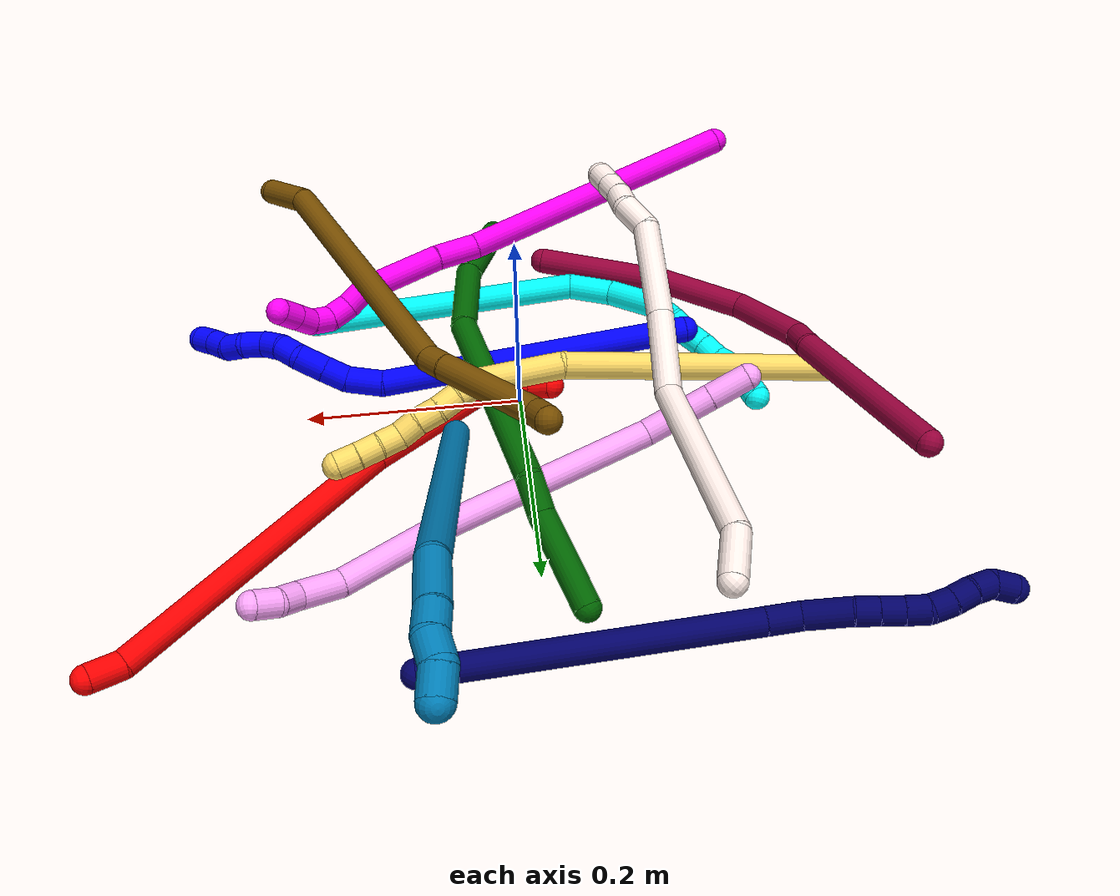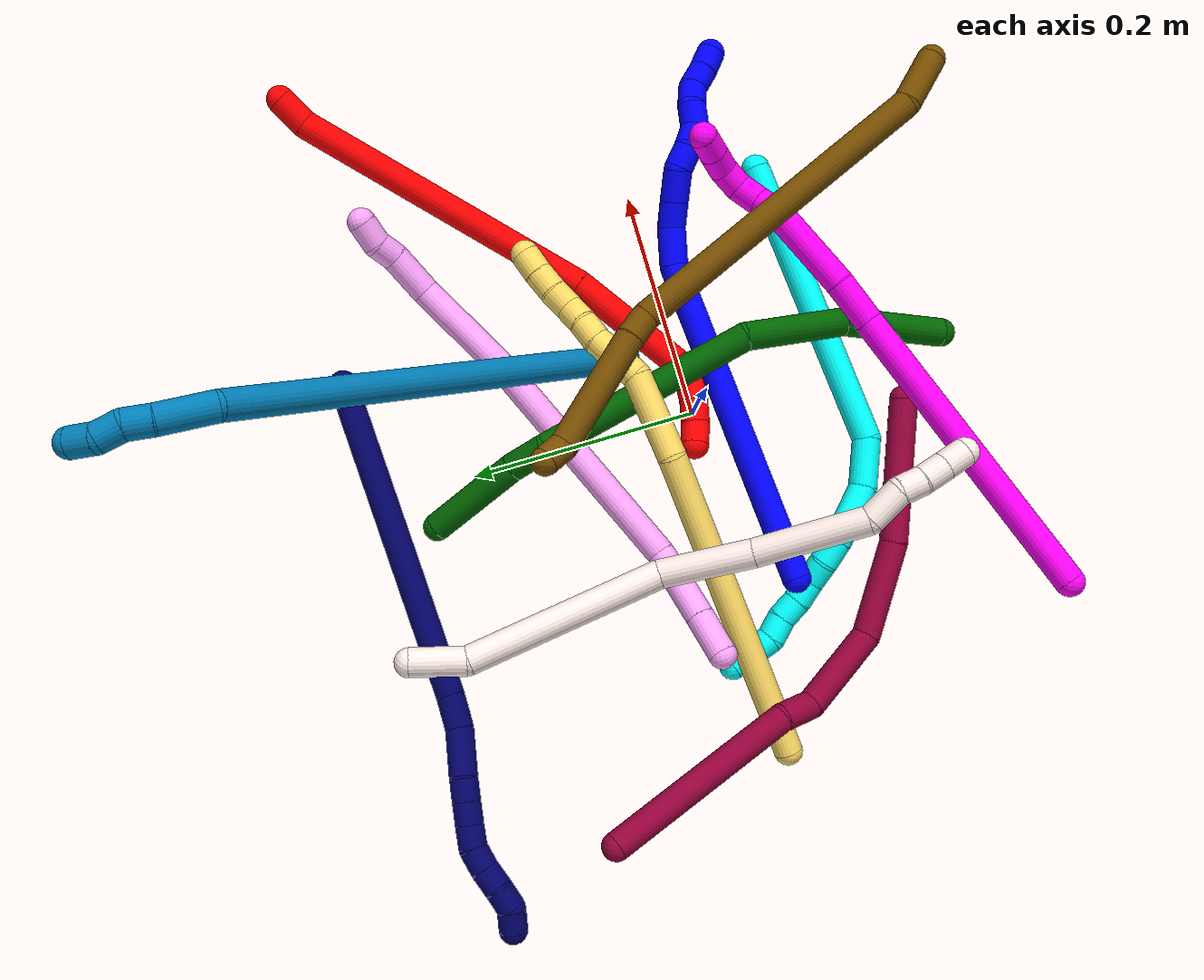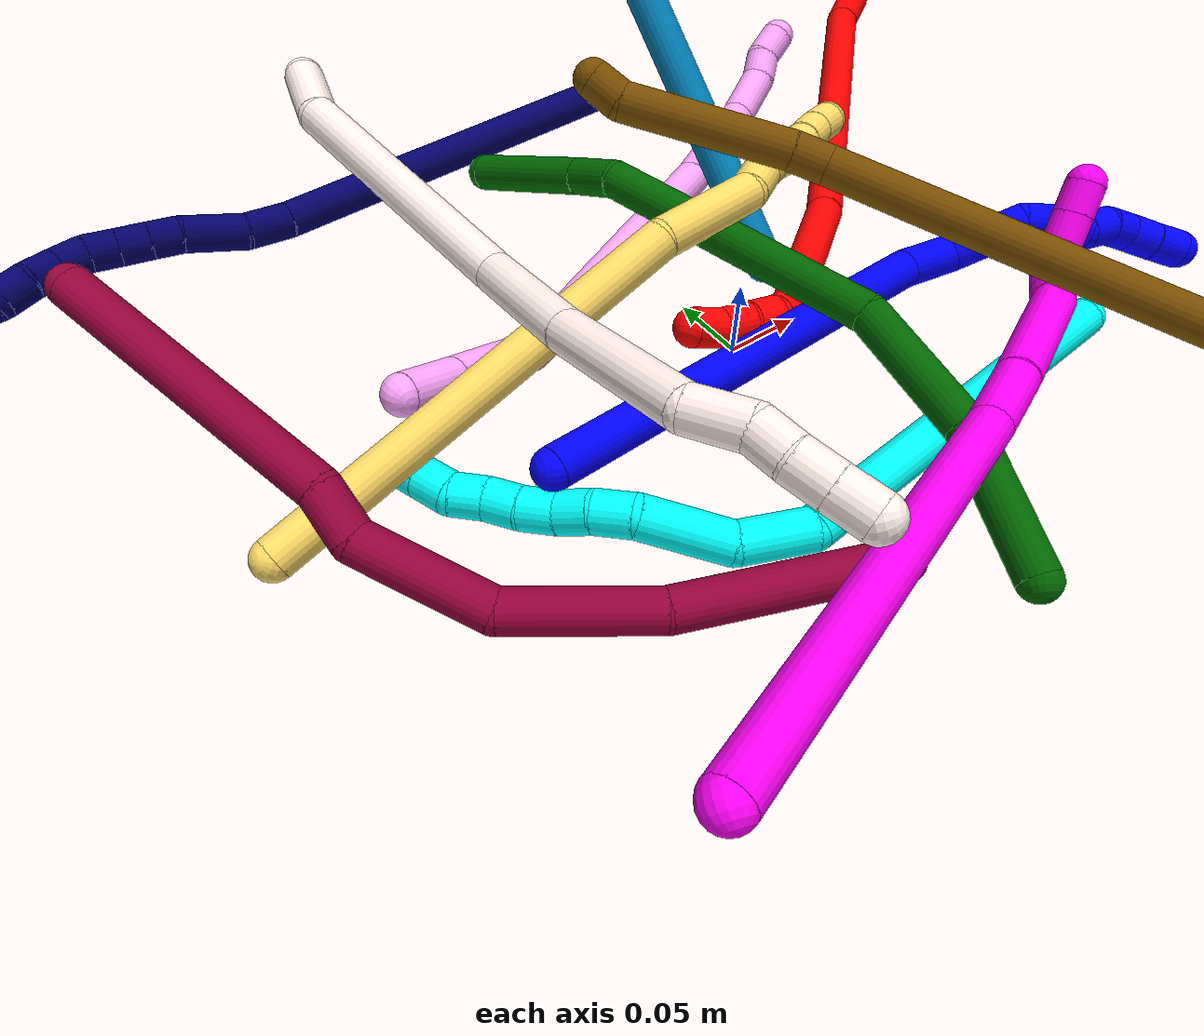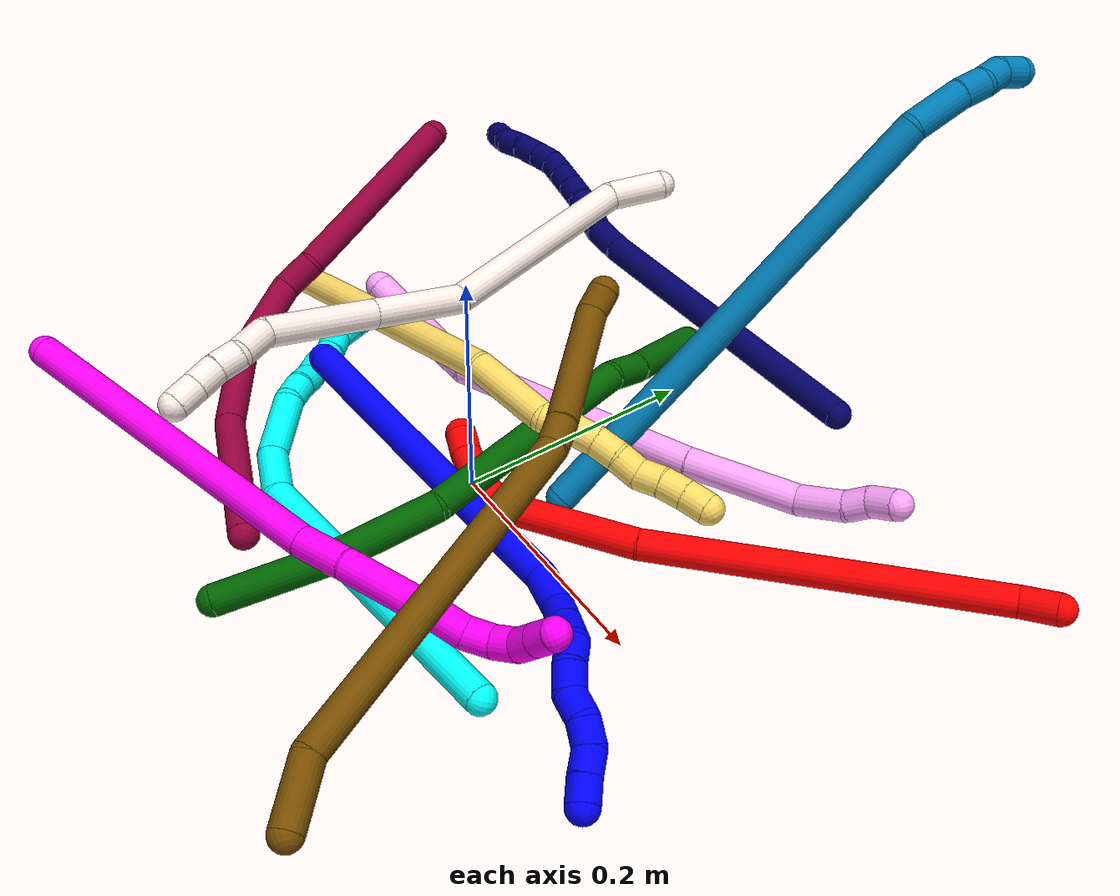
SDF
<sdf version="1.7">
 <world name="default">
  <plugin name="TubeGeneratorPlugin" filename="libtube_generator_plugin.so"/>
  <model name="photoneo_s_sensor">
   <static>1</static>
   <pose>0 0 2 1.57079 1.57079 3.14159</pose>
   <link name="link">
    <inertial><mass>0.1</mass></inertial>
    <sensor name="sensor" type="depth">
     <update_rate>30</update_rate>
     <camera>
      <horizontal_fov>1.22</horizontal_fov>
      <image><width>1920</width><height>1200</height><format>B8G8R8</format></image>
      <clip><near>0.1</near><far>4</far></clip>
      <depth_camera><output>points</output></depth_camera>
     </camera>
     <plugin name="camera_plugin" filename="libgazebo_ros_depth_camera.so">
      <baseline>0.2</baseline>
      <alwaysOn>1</alwaysOn>
      <updateRate>0.0</updateRate>
      <cameraName>camera_ir</cameraName>
      <imageTopicName>/camera/color/image_raw</imageTopicName>
      <cameraInfoTopicName>/camera/color/camera_info</cameraInfoTopicName>
      <depthImageTopicName>/camera/depth/image_raw</depthImageTopicName>
      <depthImageCameraInfoTopicName>/camera/depth/camera_info</depthImageCameraInfoTopicName>
      <pointCloudTopicName>/camera/depth/points</pointCloudTopicName>
      <frameName>fr_optical</frameName>
      <pointCloudCutoff>0.1</pointCloudCutoff>
      <pointCloudCutoffMax>2.0</pointCloudCutoffMax>
      <distortionK1>0</distortionK1>
      <distortionK2>0</distortionK2>
      <distortionK3>0</distortionK3>
      <distortionT1>0</distortionT1>
      <distortionT2>0</distortionT2>
      <CxPrime>0</CxPrime>
      <Cx>0</Cx>
      <Cy>0</Cy>
      <focalLength>0</focalLength>
      <hackBaseline>0</hackBaseline>
     </plugin>
    </sensor>
   </link>
  </model>
  <gravity>0 0 -9.8</gravity>
  <magnetic_field>6e-06 2.3e-05 -4.2e-05</magnetic_field>
  <atmosphere type="adiabatic"/>
  <physics name="default_physics" default="0" type="ode">
   <max_step_size>0.003</max_step_size>
   <real_time_factor>1</real_time_factor>
   <real_time_update_rate>1000</real_time_update_rate>
   <max_contacts>10000</max_contacts>
   <ode>
    <solver>
     <type>quick</type>
     <iters>100</iters>
     <sor>1.3</sor>
     <use_dynamic_moi_rescaling>0</use_dynamic_moi_rescaling>
    </solver>
    <constraints>
     <contact_max_correcting_vel>0</contact_max_correcting_vel>
     <contact_surface_layer>0.001</contact_surface_layer>
     <cfm>0</cfm>
     <erp>0.2</erp>
    </constraints>
   </ode>
  </physics>
  <scene><ambient>0.4 0.4 0.4 1</ambient><background>0.7 0.7 0.7 1</background><shadows>0</shadows></scene>
  <audio><device>default</device></audio>
  <spherical_coordinates>
   <surface_model>EARTH_WGS84</surface_model>
   <latitude_deg>0</latitude_deg>
   <longitude_deg>0</longitude_deg>
   <elevation>0</elevation>
   <heading_deg>0</heading_deg>
  </spherical_coordinates>
  <model name="bin">
   <static>1</static>
   <link name="bottom">
    <collision name="collision-bottom">
     <pose>0 0 -0.01 0 -0 0</pose>
     <geometry><box><size>0.8 0.6 0.02</size></box></geometry>
     <surface>
      <friction><ode><mu>100</mu><mu2>100</mu2></ode></friction>
      <contact><collide_bitmask>65535</collide_bitmask></contact>
     </surface>
    </collision>
   </link>
   <link name="west_wall">
    <collision name="collision-west_wall">
     <pose>-0.41 0 0.1 0 -0 0</pose>
     <geometry><box><size>0.02 0.6 0.2</size></box></geometry>
     <surface>
      <friction><ode><mu>100</mu><mu2>100</mu2></ode></friction>
      <contact><collide_bitmask>65535</collide_bitmask></contact>
     </surface>
    </collision>
   </link>
   <link name="east_wall">
    <collision name="collision-east_wall">
     <pose>0.41 0 0.1 0 -0 0</pose>
     <geometry><box><size>0.02 0.6 0.2</size></box></geometry>
     <surface>
      <friction><ode><mu>100</mu><mu2>100</mu2></ode></friction>
      <contact><collide_bitmask>65535</collide_bitmask></contact>
     </surface>
    </collision>
   </link>
   <link name="south_wall">
    <collision name="collision-south_wall">
     <pose>0 -0.31 0.1 0 -0 0</pose>
     <geometry><box><size>0.8 0.02 0.2</size></box></geometry>
     <surface>
      <friction><ode><mu>100</mu><mu2>100</mu2></ode></friction>
      <contact><collide_bitmask>65535</collide_bitmask></contact>
     </surface>
    </collision>
   </link>
   <link name="north_wall">
    <collision name="collision-north_wall">
     <pose>0 0.31 0.1 0 -0 0</pose>
     <geometry><box><size>0.8 0.02 0.2</size></box></geometry>
     <surface>
      <friction><ode><mu>100</mu><mu2>100</mu2></ode></friction>
      <contact><collide_bitmask>65535</collide_bitmask></contact>
     </surface>
    </collision>
   </link>
  </model>
  <model name="1">
   <static>0</static>
   <link name="1">
    <collision name="collision-cylinder-e_1_1_4">
     <pose>0.04754 0.001603 0.138305 -0.01159 0.331063 -0.001936</pose>
     <geometry><cylinder><radius>0.0125</radius><length>0.292512</length></cylinder></geometry>
     <surface>
      <friction><ode><mu>1.16</mu><mu2>1.16</mu2><slip1>0</slip1><slip2>0</slip2></ode></friction>
      <contact><ode><kp>1e+06</kp><kd>1</kd><max_vel>0</max_vel><min_depth>0.001</min_depth></ode></contact>
     </surface>
    </collision>
    <visual name="visual-cylinder-e_1_1_4">
     <pose>0.04754 0.001603 0.138305 -0.01159 0.331063 -0.001936</pose>
     <geometry><cylinder><radius>0.0125</radius><length>0.292512</length></cylinder></geometry>
     <material><ambient>0 0 1 1</ambient></material>
    </visual>
    <collision name="collision-cylinder-e_2_4_5">
     <pose>0.096014 0.006111 0.293398 -0.171361 0.054723 -0.004701</pose>
     <geometry><cylinder><radius>0.0125</radius><length>0.034127</length></cylinder></geometry>
     <surface>
      <friction><ode><mu>1.16</mu><mu2>1.16</mu2><slip1>0</slip1><slip2>0</slip2></ode></friction>
      <contact><ode><kp>1e+06</kp><kd>1</kd><max_vel>0</max_vel><min_depth>0.001</min_depth></ode></contact>
     </surface>
    </collision>
    <visual name="visual-cylinder-e_2_4_5">
     <pose>0.096014 0.006111 0.293398 -0.171361 0.054723 -0.004701</pose>
     <geometry><cylinder><radius>0.0125</radius><length>0.034127</length></cylinder></geometry>
     <material><ambient>0 0 1 1</ambient></material>
    </visual>
    <collision name="collision-cylinder-e_3_5_6">
     <pose>0.096236 0.014344 0.320537 -0.475344 -0.061036 0.01479</pose>
     <geometry><cylinder><radius>0.0125</radius><length>0.023327</length></cylinder></geometry>
     <surface>
      <friction><ode><mu>1.16</mu><mu2>1.16</mu2><slip1>0</slip1><slip2>0</slip2></ode></friction>
      <contact><ode><kp>1e+06</kp><kd>1</kd><max_vel>0</max_vel><min_depth>0.001</min_depth></ode></contact>
     </surface>
    </collision>
    <visual name="visual-cylinder-e_3_5_6">
     <pose>0.096236 0.014344 0.320537 -0.475344 -0.061036 0.01479</pose>
     <geometry><cylinder><radius>0.0125</radius><length>0.023327</length></cylinder></geometry>
     <material><ambient>0 0 1 1</ambient></material>
    </visual>
    <collision name="collision-cylinder-e_4_6_7">
     <pose>0.09453 0.026206 0.34293 -0.497127 -0.072455 0.018398</pose>
     <geometry><cylinder><radius>0.0125</radius><length>0.027472</length></cylinder></geometry>
     <surface>
      <friction><ode><mu>1.16</mu><mu2>1.16</mu2><slip1>0</slip1><slip2>0</slip2></ode></friction>
      <contact><ode><kp>1e+06</kp><kd>1</kd><max_vel>0</max_vel><min_depth>0.001</min_depth></ode></contact>
     </surface>
    </collision>
    <visual name="visual-cylinder-e_4_6_7">
     <pose>0.09453 0.026206 0.34293 -0.497127 -0.072455 0.018398</pose>
     <geometry><cylinder><radius>0.0125</radius><length>0.027472</length></cylinder></geometry>
     <material><ambient>0 0 1 1</ambient></material>
    </visual>
    <collision name="collision-cylinder-e_5_7_8">
     <pose>0.089085 0.034671 0.363975 -0.211308 -0.45022 0.048559</pose>
     <geometry><cylinder><radius>0.0125</radius><length>0.020453</length></cylinder></geometry>
     <surface>
      <friction><ode><mu>1.16</mu><mu2>1.16</mu2><slip1>0</slip1><slip2>0</slip2></ode></friction>
      <contact><ode><kp>1e+06</kp><kd>1</kd><max_vel>0</max_vel><min_depth>0.001</min_depth></ode></contact>
     </surface>
    </collision>
    <visual name="visual-cylinder-e_5_7_8">
     <pose>0.089085 0.034671 0.363975 -0.211308 -0.45022 0.048559</pose>
     <geometry><cylinder><radius>0.0125</radius><length>0.020453</length></cylinder></geometry>
     <material><ambient>0 0 1 1</ambient></material>
    </visual>
    <collision name="collision-cylinder-e_6_8_9">
     <pose>0.080836 0.035483 0.382633 0.115363 -0.372576 -0.021766</pose>
     <geometry><cylinder><radius>0.0125</radius><length>0.020874</length></cylinder></geometry>
     <surface>
      <friction><ode><mu>1.16</mu><mu2>1.16</mu2><slip1>0</slip1><slip2>0</slip2></ode></friction>
      <contact><ode><kp>1e+06</kp><kd>1</kd><max_vel>0</max_vel><min_depth>0.001</min_depth></ode></contact>
     </surface>
    </collision>
    <visual name="visual-cylinder-e_6_8_9">
     <pose>0.080836 0.035483 0.382633 0.115363 -0.372576 -0.021766</pose>
     <geometry><cylinder><radius>0.0125</radius><length>0.020874</length></cylinder></geometry>
     <material><ambient>0 0 1 1</ambient></material>
    </visual>
    <collision name="collision-cylinder-e_7_9_10">
     <pose>0.078004 0.034369 0.402793 -0.000437 0.091826 -2e-05</pose>
     <geometry><cylinder><radius>0.0125</radius><length>0.021096</length></cylinder></geometry>
     <surface>
      <friction><ode><mu>1.16</mu><mu2>1.16</mu2><slip1>0</slip1><slip2>0</slip2></ode></friction>
      <contact><ode><kp>1e+06</kp><kd>1</kd><max_vel>0</max_vel><min_depth>0.001</min_depth></ode></contact>
     </surface>
    </collision>
    <visual name="visual-cylinder-e_7_9_10">
     <pose>0.078004 0.034369 0.402793 -0.000437 0.091826 -2e-05</pose>
     <geometry><cylinder><radius>0.0125</radius><length>0.021096</length></cylinder></geometry>
     <material><ambient>0 0 1 1</ambient></material>
    </visual>
    <collision name="collision-cylinder-e_8_10_11">
     <pose>0.077546 0.031514 0.422815 0.291873 -0.14245 -0.020972</pose>
     <geometry><cylinder><radius>0.0125</radius><length>0.02008</length></cylinder></geometry>
     <surface>
      <friction><ode><mu>1.16</mu><mu2>1.16</mu2><slip1>0</slip1><slip2>0</slip2></ode></friction>
      <contact><ode><kp>1e+06</kp><kd>1</kd><max_vel>0</max_vel><min_depth>0.001</min_depth></ode></contact>
     </surface>
    </collision>
    <visual name="visual-cylinder-e_8_10_11">
     <pose>0.077546 0.031514 0.422815 0.291873 -0.14245 -0.020972</pose>
     <geometry><cylinder><radius>0.0125</radius><length>0.02008</length></cylinder></geometry>
     <material><ambient>0 0 1 1</ambient></material>
    </visual>
    <collision name="collision-cylinder-e_9_11_12">
     <pose>0.070985 0.027719 0.440887 0.108919 -0.538051 -0.030057</pose>
     <geometry><cylinder><radius>0.0125</radius><length>0.020041</length></cylinder></geometry>
     <surface>
      <friction><ode><mu>1.16</mu><mu2>1.16</mu2><slip1>0</slip1><slip2>0</slip2></ode></friction>
      <contact><ode><kp>1e+06</kp><kd>1</kd><max_vel>0</max_vel><min_depth>0.001</min_depth></ode></contact>
     </surface>
    </collision>
    <visual name="visual-cylinder-e_9_11_12">
     <pose>0.070985 0.027719 0.440887 0.108919 -0.538051 -0.030057</pose>
     <geometry><cylinder><radius>0.0125</radius><length>0.020041</length></cylinder></geometry>
     <material><ambient>0 0 1 1</ambient></material>
    </visual>
    <collision name="collision-cylinder-e_10_12_2">
     <pose>0.061575 0.025608 0.458413 0.130274 -0.441338 -0.029263</pose>
     <geometry><cylinder><radius>0.0125</radius><length>0.020018</length></cylinder></geometry>
     <surface>
      <friction><ode><mu>1.16</mu><mu2>1.16</mu2><slip1>0</slip1><slip2>0</slip2></ode></friction>
      <contact><ode><kp>1e+06</kp><kd>1</kd><max_vel>0</max_vel><min_depth>0.001</min_depth></ode></contact>
     </surface>
    </collision>
    <visual name="visual-cylinder-e_10_12_2">
     <pose>0.061575 0.025608 0.458413 0.130274 -0.441338 -0.029263</pose>
     <geometry><cylinder><radius>0.0125</radius><length>0.020018</length></cylinder></geometry>
     <material><ambient>0 0 1 1</ambient></material>
    </visual>
    <collision name="collision-sphere-2">
     <pose>0.0573 0.024432 0.467387 0 -0 0</pose>
     <geometry><sphere><radius>0.0125</radius></sphere></geometry>
     <surface>
      <friction><ode><mu>1.16</mu><mu2>1.16</mu2><slip1>0</slip1><slip2>0</slip2></ode></friction>
      <contact><ode><kp>1e+06</kp><kd>1</kd><max_vel>0</max_vel><min_depth>0.001</min_depth></ode></contact>
     </surface>
    </collision>
    <visual name="visual-sphere-2">
     <pose>0.0573 0.024432 0.467387 0 -0 0</pose>
     <geometry><sphere><radius>0.0125</radius></sphere></geometry>
     <material><ambient>0 0 1 1</ambient></material>
    </visual>
    <collision name="collision-sphere-12">
     <pose>0.06585 0.026783 0.44944 0 -0 0</pose>
     <geometry><sphere><radius>0.0125</radius></sphere></geometry>
     <surface>
      <friction><ode><mu>1.16</mu><mu2>1.16</mu2><slip1>0</slip1><slip2>0</slip2></ode></friction>
      <contact><ode><kp>1e+06</kp><kd>1</kd><max_vel>0</max_vel><min_depth>0.001</min_depth></ode></contact>
     </surface>
    </collision>
    <visual name="visual-sphere-12">
     <pose>0.06585 0.026783 0.44944 0 -0 0</pose>
     <geometry><sphere><radius>0.0125</radius></sphere></geometry>
     <material><ambient>0 0 1 1</ambient></material>
    </visual>
    <collision name="collision-sphere-11">
     <pose>0.07612 0.028654 0.432333 0 -0 0</pose>
     <geometry><sphere><radius>0.0125</radius></sphere></geometry>
     <surface>
      <friction><ode><mu>1.16</mu><mu2>1.16</mu2><slip1>0</slip1><slip2>0</slip2></ode></friction>
      <contact><ode><kp>1e+06</kp><kd>1</kd><max_vel>0</max_vel><min_depth>0.001</min_depth></ode></contact>
     </surface>
    </collision>
    <visual name="visual-sphere-11">
     <pose>0.07612 0.028654 0.432333 0 -0 0</pose>
     <geometry><sphere><radius>0.0125</radius></sphere></geometry>
     <material><ambient>0 0 1 1</ambient></material>
    </visual>
    <collision name="collision-sphere-10">
     <pose>0.078971 0.034373 0.413297 0 -0 0</pose>
     <geometry><sphere><radius>0.0125</radius></sphere></geometry>
     <surface>
      <friction><ode><mu>1.16</mu><mu2>1.16</mu2><slip1>0</slip1><slip2>0</slip2></ode></friction>
      <contact><ode><kp>1e+06</kp><kd>1</kd><max_vel>0</max_vel><min_depth>0.001</min_depth></ode></contact>
     </surface>
    </collision>
    <visual name="visual-sphere-10">
     <pose>0.078971 0.034373 0.413297 0 -0 0</pose>
     <geometry><sphere><radius>0.0125</radius></sphere></geometry>
     <material><ambient>0 0 1 1</ambient></material>
    </visual>
    <collision name="collision-sphere-9">
     <pose>0.077037 0.034364 0.39229 0 -0 0</pose>
     <geometry><sphere><radius>0.0125</radius></sphere></geometry>
     <surface>
      <friction><ode><mu>1.16</mu><mu2>1.16</mu2><slip1>0</slip1><slip2>0</slip2></ode></friction>
      <contact><ode><kp>1e+06</kp><kd>1</kd><max_vel>0</max_vel><min_depth>0.001</min_depth></ode></contact>
     </surface>
    </collision>
    <visual name="visual-sphere-9">
     <pose>0.077037 0.034364 0.39229 0 -0 0</pose>
     <geometry><sphere><radius>0.0125</radius></sphere></geometry>
     <material><ambient>0 0 1 1</ambient></material>
    </visual>
    <collision name="collision-sphere-4">
     <pose>0.095081 0.003206 0.276609 0 -0 0</pose>
     <geometry><sphere><radius>0.0125</radius></sphere></geometry>
     <surface>
      <friction><ode><mu>1.16</mu><mu2>1.16</mu2><slip1>0</slip1><slip2>0</slip2></ode></friction>
      <contact><ode><kp>1e+06</kp><kd>1</kd><max_vel>0</max_vel><min_depth>0.001</min_depth></ode></contact>
     </surface>
    </collision>
    <visual name="visual-sphere-4">
     <pose>0.095081 0.003206 0.276609 0 -0 0</pose>
     <geometry><sphere><radius>0.0125</radius></sphere></geometry>
     <material><ambient>0 0 1 1</ambient></material>
    </visual>
    <collision name="collision-sphere-1">
     <geometry><sphere><radius>0.0125</radius></sphere></geometry>
     <surface>
      <friction><ode><mu>1.16</mu><mu2>1.16</mu2><slip1>0</slip1><slip2>0</slip2></ode></friction>
      <contact><ode><kp>1e+06</kp><kd>1</kd><max_vel>0</max_vel><min_depth>0.001</min_depth></ode></contact>
     </surface>
    </collision>
    <visual name="visual-sphere-1">
     <geometry><sphere><radius>0.0125</radius></sphere></geometry>
     <material><ambient>0 0 1 1</ambient></material>
    </visual>
    <collision name="collision-sphere-8">
     <pose>0.084635 0.036602 0.372977 0 -0 0</pose>
     <geometry><sphere><radius>0.0125</radius></sphere></geometry>
     <surface>
      <friction><ode><mu>1.16</mu><mu2>1.16</mu2><slip1>0</slip1><slip2>0</slip2></ode></friction>
      <contact><ode><kp>1e+06</kp><kd>1</kd><max_vel>0</max_vel><min_depth>0.001</min_depth></ode></contact>
     </surface>
    </collision>
    <visual name="visual-sphere-8">
     <pose>0.084635 0.036602 0.372977 0 -0 0</pose>
     <geometry><sphere><radius>0.0125</radius></sphere></geometry>
     <material><ambient>0 0 1 1</ambient></material>
    </visual>
    <collision name="collision-sphere-5">
     <pose>0.096947 0.009017 0.310186 0 -0 0</pose>
     <geometry><sphere><radius>0.0125</radius></sphere></geometry>
     <surface>
      <friction><ode><mu>1.16</mu><mu2>1.16</mu2><slip1>0</slip1><slip2>0</slip2></ode></friction>
      <contact><ode><kp>1e+06</kp><kd>1</kd><max_vel>0</max_vel><min_depth>0.001</min_depth></ode></contact>
     </surface>
    </collision>
    <visual name="visual-sphere-5">
     <pose>0.096947 0.009017 0.310186 0 -0 0</pose>
     <geometry><sphere><radius>0.0125</radius></sphere></geometry>
     <material><ambient>0 0 1 1</ambient></material>
    </visual>
    <collision name="collision-sphere-6">
     <pose>0.095524 0.019672 0.330888 0 -0 0</pose>
     <geometry><sphere><radius>0.0125</radius></sphere></geometry>
     <surface>
      <friction><ode><mu>1.16</mu><mu2>1.16</mu2><slip1>0</slip1><slip2>0</slip2></ode></friction>
      <contact><ode><kp>1e+06</kp><kd>1</kd><max_vel>0</max_vel><min_depth>0.001</min_depth></ode></contact>
     </surface>
    </collision>
    <visual name="visual-sphere-6">
     <pose>0.095524 0.019672 0.330888 0 -0 0</pose>
     <geometry><sphere><radius>0.0125</radius></sphere></geometry>
     <material><ambient>0 0 1 1</ambient></material>
    </visual>
    <collision name="collision-sphere-7">
     <pose>0.093536 0.03274 0.354972 0 -0 0</pose>
     <geometry><sphere><radius>0.0125</radius></sphere></geometry>
     <surface>
      <friction><ode><mu>1.16</mu><mu2>1.16</mu2><slip1>0</slip1><slip2>0</slip2></ode></friction>
      <contact><ode><kp>1e+06</kp><kd>1</kd><max_vel>0</max_vel><min_depth>0.001</min_depth></ode></contact>
     </surface>
    </collision>
    <visual name="visual-sphere-7">
     <pose>0.093536 0.03274 0.354972 0 -0 0</pose>
     <geometry><sphere><radius>0.0125</radius></sphere></geometry>
     <material><ambient>0 0 1 1</ambient></material>
    </visual>
    <inertial>
     <pose>0.062784 0.011215 0.235596 0 -0 0</pose>
     <mass>0.5</mass>
     <inertia>
      <ixx>0.002002</ixx>
      <ixy>0</ixy>
      <ixz>0</ixz>
      <iyy>0.002113</iyy>
      <iyz>0</iyz>
      <izz>-0.000668</izz>
     </inertia>
    </inertial>
   </link>
   <pose>-0.164016 -0.043023 0.035719 1.69335 -0.150392 1.30485</pose>
  </model>
  <model name="2">
   <static>0</static>
   <link name="2">
    <collision name="collision-cylinder-e_1_1_4">
     <pose>-0.003413 -0.002862 -0.014145 2.94198 -0.232242 -1.72277</pose>
     <geometry><cylinder><radius>0.0125</radius><length>0.029659</length></cylinder></geometry>
     <surface>
      <friction><ode><mu>1.16</mu><mu2>1.16</mu2><slip1>0</slip1><slip2>0</slip2></ode></friction>
      <contact><ode><kp>1e+06</kp><kd>1</kd><max_vel>0</max_vel><min_depth>0.001</min_depth></ode></contact>
     </surface>
    </collision>
    <visual name="visual-cylinder-e_1_1_4">
     <pose>-0.003413 -0.002862 -0.014145 2.94198 -0.232242 -1.72277</pose>
     <geometry><cylinder><radius>0.0125</radius><length>0.029659</length></cylinder></geometry>
     <material><ambient>1 0 0 1</ambient></material>
    </visual>
    <collision name="collision-cylinder-e_2_4_5">
     <pose>-0.029843 -0.07486 -0.148525 2.61975 -0.16445 -0.598732</pose>
     <geometry><cylinder><radius>0.0125</radius><length>0.281184</length></cylinder></geometry>
     <surface>
      <friction><ode><mu>1.16</mu><mu2>1.16</mu2><slip1>0</slip1><slip2>0</slip2></ode></friction>
      <contact><ode><kp>1e+06</kp><kd>1</kd><max_vel>0</max_vel><min_depth>0.001</min_depth></ode></contact>
     </surface>
    </collision>
    <visual name="visual-cylinder-e_2_4_5">
     <pose>-0.029843 -0.07486 -0.148525 2.61975 -0.16445 -0.598732</pose>
     <geometry><cylinder><radius>0.0125</radius><length>0.281184</length></cylinder></geometry>
     <material><ambient>1 0 0 1</ambient></material>
    </visual>
    <collision name="collision-cylinder-e_3_5_6">
     <pose>-0.068632 -0.166262 -0.315917 2.70049 -0.293714 -1.16643</pose>
     <geometry><cylinder><radius>0.0125</radius><length>0.108965</length></cylinder></geometry>
     <surface>
      <friction><ode><mu>1.16</mu><mu2>1.16</mu2><slip1>0</slip1><slip2>0</slip2></ode></friction>
      <contact><ode><kp>1e+06</kp><kd>1</kd><max_vel>0</max_vel><min_depth>0.001</min_depth></ode></contact>
     </surface>
    </collision>
    <visual name="visual-cylinder-e_3_5_6">
     <pose>-0.068632 -0.166262 -0.315917 2.70049 -0.293714 -1.16643</pose>
     <geometry><cylinder><radius>0.0125</radius><length>0.108965</length></cylinder></geometry>
     <material><ambient>1 0 0 1</ambient></material>
    </visual>
    <collision name="collision-cylinder-e_4_6_7">
     <pose>-0.091101 -0.192611 -0.369299 2.56093 -0.732546 -1.81811</pose>
     <geometry><cylinder><radius>0.0125</radius><length>0.020025</length></cylinder></geometry>
     <surface>
      <friction><ode><mu>1.16</mu><mu2>1.16</mu2><slip1>0</slip1><slip2>0</slip2></ode></friction>
      <contact><ode><kp>1e+06</kp><kd>1</kd><max_vel>0</max_vel><min_depth>0.001</min_depth></ode></contact>
     </surface>
    </collision>
    <visual name="visual-cylinder-e_4_6_7">
     <pose>-0.091101 -0.192611 -0.369299 2.56093 -0.732546 -1.81811</pose>
     <geometry><cylinder><radius>0.0125</radius><length>0.020025</length></cylinder></geometry>
     <material><ambient>1 0 0 1</ambient></material>
    </visual>
    <collision name="collision-cylinder-e_5_7_8">
     <pose>-0.105878 -0.19688 -0.381474 3.11039 -0.935757 -3.07985</pose>
     <geometry><cylinder><radius>0.0125</radius><length>0.020076</length></cylinder></geometry>
     <surface>
      <friction><ode><mu>1.16</mu><mu2>1.16</mu2><slip1>0</slip1><slip2>0</slip2></ode></friction>
      <contact><ode><kp>1e+06</kp><kd>1</kd><max_vel>0</max_vel><min_depth>0.001</min_depth></ode></contact>
     </surface>
    </collision>
    <visual name="visual-cylinder-e_5_7_8">
     <pose>-0.105878 -0.19688 -0.381474 3.11039 -0.935757 -3.07985</pose>
     <geometry><cylinder><radius>0.0125</radius><length>0.020076</length></cylinder></geometry>
     <material><ambient>1 0 0 1</ambient></material>
    </visual>
    <collision name="collision-cylinder-e_6_8_9">
     <pose>-0.121774 -0.195439 -0.393465 -2.8785 -0.895902 2.60423</pose>
     <geometry><cylinder><radius>0.0125</radius><length>0.020018</length></cylinder></geometry>
     <surface>
      <friction><ode><mu>1.16</mu><mu2>1.16</mu2><slip1>0</slip1><slip2>0</slip2></ode></friction>
      <contact><ode><kp>1e+06</kp><kd>1</kd><max_vel>0</max_vel><min_depth>0.001</min_depth></ode></contact>
     </surface>
    </collision>
    <visual name="visual-cylinder-e_6_8_9">
     <pose>-0.121774 -0.195439 -0.393465 -2.8785 -0.895902 2.60423</pose>
     <geometry><cylinder><radius>0.0125</radius><length>0.020018</length></cylinder></geometry>
     <material><ambient>1 0 0 1</ambient></material>
    </visual>
    <collision name="collision-cylinder-e_7_9_2">
     <pose>-0.138675 -0.192649 -0.403604 -2.86514 -1.13216 2.71055</pose>
     <geometry><cylinder><radius>0.0125</radius><length>0.020073</length></cylinder></geometry>
     <surface>
      <friction><ode><mu>1.16</mu><mu2>1.16</mu2><slip1>0</slip1><slip2>0</slip2></ode></friction>
      <contact><ode><kp>1e+06</kp><kd>1</kd><max_vel>0</max_vel><min_depth>0.001</min_depth></ode></contact>
     </surface>
    </collision>
    <visual name="visual-cylinder-e_7_9_2">
     <pose>-0.138675 -0.192649 -0.403604 -2.86514 -1.13216 2.71055</pose>
     <geometry><cylinder><radius>0.0125</radius><length>0.020073</length></cylinder></geometry>
     <material><ambient>1 0 0 1</ambient></material>
    </visual>
    <collision name="collision-sphere-2">
     <pose>-0.147761 -0.191486 -0.407705 0 -0 0</pose>
     <geometry><sphere><radius>0.0125</radius></sphere></geometry>
     <surface>
      <friction><ode><mu>1.16</mu><mu2>1.16</mu2><slip1>0</slip1><slip2>0</slip2></ode></friction>
      <contact><ode><kp>1e+06</kp><kd>1</kd><max_vel>0</max_vel><min_depth>0.001</min_depth></ode></contact>
     </surface>
    </collision>
    <visual name="visual-sphere-2">
     <pose>-0.147761 -0.191486 -0.407705 0 -0 0</pose>
     <geometry><sphere><radius>0.0125</radius></sphere></geometry>
     <material><ambient>1 0 0 1</ambient></material>
    </visual>
    <collision name="collision-sphere-9">
     <pose>-0.129589 -0.193813 -0.399503 0 -0 0</pose>
     <geometry><sphere><radius>0.0125</radius></sphere></geometry>
     <surface>
      <friction><ode><mu>1.16</mu><mu2>1.16</mu2><slip1>0</slip1><slip2>0</slip2></ode></friction>
      <contact><ode><kp>1e+06</kp><kd>1</kd><max_vel>0</max_vel><min_depth>0.001</min_depth></ode></contact>
     </surface>
    </collision>
    <visual name="visual-sphere-9">
     <pose>-0.129589 -0.193813 -0.399503 0 -0 0</pose>
     <geometry><sphere><radius>0.0125</radius></sphere></geometry>
     <material><ambient>1 0 0 1</ambient></material>
    </visual>
    <collision name="collision-sphere-4">
     <pose>-0.006826 -0.005723 -0.02829 0 -0 0</pose>
     <geometry><sphere><radius>0.0125</radius></sphere></geometry>
     <surface>
      <friction><ode><mu>1.16</mu><mu2>1.16</mu2><slip1>0</slip1><slip2>0</slip2></ode></friction>
      <contact><ode><kp>1e+06</kp><kd>1</kd><max_vel>0</max_vel><min_depth>0.001</min_depth></ode></contact>
     </surface>
    </collision>
    <visual name="visual-sphere-4">
     <pose>-0.006826 -0.005723 -0.02829 0 -0 0</pose>
     <geometry><sphere><radius>0.0125</radius></sphere></geometry>
     <material><ambient>1 0 0 1</ambient></material>
    </visual>
    <collision name="collision-sphere-1">
     <geometry><sphere><radius>0.0125</radius></sphere></geometry>
     <surface>
      <friction><ode><mu>1.16</mu><mu2>1.16</mu2><slip1>0</slip1><slip2>0</slip2></ode></friction>
      <contact><ode><kp>1e+06</kp><kd>1</kd><max_vel>0</max_vel><min_depth>0.001</min_depth></ode></contact>
     </surface>
    </collision>
    <visual name="visual-sphere-1">
     <geometry><sphere><radius>0.0125</radius></sphere></geometry>
     <material><ambient>1 0 0 1</ambient></material>
    </visual>
    <collision name="collision-sphere-8">
     <pose>-0.113959 -0.197066 -0.387426 0 -0 0</pose>
     <geometry><sphere><radius>0.0125</radius></sphere></geometry>
     <surface>
      <friction><ode><mu>1.16</mu><mu2>1.16</mu2><slip1>0</slip1><slip2>0</slip2></ode></friction>
      <contact><ode><kp>1e+06</kp><kd>1</kd><max_vel>0</max_vel><min_depth>0.001</min_depth></ode></contact>
     </surface>
    </collision>
    <visual name="visual-sphere-8">
     <pose>-0.113959 -0.197066 -0.387426 0 -0 0</pose>
     <geometry><sphere><radius>0.0125</radius></sphere></geometry>
     <material><ambient>1 0 0 1</ambient></material>
    </visual>
    <collision name="collision-sphere-5">
     <pose>-0.052859 -0.143998 -0.26876 0 -0 0</pose>
     <geometry><sphere><radius>0.0125</radius></sphere></geometry>
     <surface>
      <friction><ode><mu>1.16</mu><mu2>1.16</mu2><slip1>0</slip1><slip2>0</slip2></ode></friction>
      <contact><ode><kp>1e+06</kp><kd>1</kd><max_vel>0</max_vel><min_depth>0.001</min_depth></ode></contact>
     </surface>
    </collision>
    <visual name="visual-sphere-5">
     <pose>-0.052859 -0.143998 -0.26876 0 -0 0</pose>
     <geometry><sphere><radius>0.0125</radius></sphere></geometry>
     <material><ambient>1 0 0 1</ambient></material>
    </visual>
    <collision name="collision-sphere-6">
     <pose>-0.084405 -0.188527 -0.363075 0 -0 0</pose>
     <geometry><sphere><radius>0.0125</radius></sphere></geometry>
     <surface>
      <friction><ode><mu>1.16</mu><mu2>1.16</mu2><slip1>0</slip1><slip2>0</slip2></ode></friction>
      <contact><ode><kp>1e+06</kp><kd>1</kd><max_vel>0</max_vel><min_depth>0.001</min_depth></ode></contact>
     </surface>
    </collision>
    <visual name="visual-sphere-6">
     <pose>-0.084405 -0.188527 -0.363075 0 -0 0</pose>
     <geometry><sphere><radius>0.0125</radius></sphere></geometry>
     <material><ambient>1 0 0 1</ambient></material>
    </visual>
    <collision name="collision-sphere-7">
     <pose>-0.097797 -0.196694 -0.375523 0 -0 0</pose>
     <geometry><sphere><radius>0.0125</radius></sphere></geometry>
     <surface>
      <friction><ode><mu>1.16</mu><mu2>1.16</mu2><slip1>0</slip1><slip2>0</slip2></ode></friction>
      <contact><ode><kp>1e+06</kp><kd>1</kd><max_vel>0</max_vel><min_depth>0.001</min_depth></ode></contact>
     </surface>
    </collision>
    <visual name="visual-sphere-7">
     <pose>-0.097797 -0.196694 -0.375523 0 -0 0</pose>
     <geometry><sphere><radius>0.0125</radius></sphere></geometry>
     <material><ambient>1 0 0 1</ambient></material>
    </visual>
    <inertial>
     <pose>-0.050284 -0.10968 -0.215275 0 -0 0</pose>
     <mass>0.5</mass>
     <inertia>
      <ixx>0.000408</ixx>
      <ixy>0</ixy>
      <ixz>0</ixz>
      <iyy>-0.002424</iyy>
      <iyz>0</iyz>
      <izz>0.001274</izz>
     </inertia>
    </inertial>
   </link>
   <pose>0.365877 0.270347 0.024046 -0.905475 0.620976 -0.596148</pose>
  </model>
  <model name="3">
   <static>0</static>
   <link name="3">
    <collision name="collision-cylinder-e_1_1_4">
     <pose>-0.118309 0.014249 0.049085 -0.282535 -1.163 0.186417</pose>
     <geometry><cylinder><radius>0.0125</radius><length>0.257754</length></cylinder></geometry>
     <surface>
      <friction><ode><mu>1.16</mu><mu2>1.16</mu2><slip1>0</slip1><slip2>0</slip2></ode></friction>
      <contact><ode><kp>1e+06</kp><kd>1</kd><max_vel>0</max_vel><min_depth>0.001</min_depth></ode></contact>
     </surface>
    </collision>
    <visual name="visual-cylinder-e_1_1_4">
     <pose>-0.118309 0.014249 0.049085 -0.282535 -1.163 0.186417</pose>
     <geometry><cylinder><radius>0.0125</radius><length>0.257754</length></cylinder></geometry>
     <material><ambient>0.003922 1 0.996078 1</ambient></material>
    </visual>
    <collision name="collision-cylinder-e_2_4_5">
     <pose>-0.25705 0.036695 0.098022 -1.58889 -1.18926 1.20611</pose>
     <geometry><cylinder><radius>0.0125</radius><length>0.044031</length></cylinder></geometry>
     <surface>
      <friction><ode><mu>1.16</mu><mu2>1.16</mu2><slip1>0</slip1><slip2>0</slip2></ode></friction>
      <contact><ode><kp>1e+06</kp><kd>1</kd><max_vel>0</max_vel><min_depth>0.001</min_depth></ode></contact>
     </surface>
    </collision>
    <visual name="visual-cylinder-e_2_4_5">
     <pose>-0.25705 0.036695 0.098022 -1.58889 -1.18926 1.20611</pose>
     <geometry><cylinder><radius>0.0125</radius><length>0.044031</length></cylinder></geometry>
     <material><ambient>0.003922 1 0.996078 1</ambient></material>
    </visual>
    <collision name="collision-cylinder-e_3_5_6">
     <pose>-0.296016 0.063023 0.091888 -1.88964 -0.770513 1.02236</pose>
     <geometry><cylinder><radius>0.0125</radius><length>0.05322</length></cylinder></geometry>
     <surface>
      <friction><ode><mu>1.16</mu><mu2>1.16</mu2><slip1>0</slip1><slip2>0</slip2></ode></friction>
      <contact><ode><kp>1e+06</kp><kd>1</kd><max_vel>0</max_vel><min_depth>0.001</min_depth></ode></contact>
     </surface>
    </collision>
    <visual name="visual-cylinder-e_3_5_6">
     <pose>-0.296016 0.063023 0.091888 -1.88964 -0.770513 1.02236</pose>
     <geometry><cylinder><radius>0.0125</radius><length>0.05322</length></cylinder></geometry>
     <material><ambient>0.003922 1 0.996078 1</ambient></material>
    </visual>
    <collision name="collision-cylinder-e_4_6_7">
     <pose>-0.323456 0.085697 0.080314 -2.45907 -0.890805 1.86236</pose>
     <geometry><cylinder><radius>0.0125</radius><length>0.022905</length></cylinder></geometry>
     <surface>
      <friction><ode><mu>1.16</mu><mu2>1.16</mu2><slip1>0</slip1><slip2>0</slip2></ode></friction>
      <contact><ode><kp>1e+06</kp><kd>1</kd><max_vel>0</max_vel><min_depth>0.001</min_depth></ode></contact>
     </surface>
    </collision>
    <visual name="visual-cylinder-e_4_6_7">
     <pose>-0.323456 0.085697 0.080314 -2.45907 -0.890805 1.86236</pose>
     <geometry><cylinder><radius>0.0125</radius><length>0.022905</length></cylinder></geometry>
     <material><ambient>0.003922 1 0.996078 1</ambient></material>
    </visual>
    <collision name="collision-cylinder-e_5_7_8">
     <pose>-0.340398 0.092194 0.068848 -2.82039 -0.914156 2.50521</pose>
     <geometry><cylinder><radius>0.0125</radius><length>0.020295</length></cylinder></geometry>
     <surface>
      <friction><ode><mu>1.16</mu><mu2>1.16</mu2><slip1>0</slip1><slip2>0</slip2></ode></friction>
      <contact><ode><kp>1e+06</kp><kd>1</kd><max_vel>0</max_vel><min_depth>0.001</min_depth></ode></contact>
     </surface>
    </collision>
    <visual name="visual-cylinder-e_5_7_8">
     <pose>-0.340398 0.092194 0.068848 -2.82039 -0.914156 2.50521</pose>
     <geometry><cylinder><radius>0.0125</radius><length>0.020295</length></cylinder></geometry>
     <material><ambient>0.003922 1 0.996078 1</ambient></material>
    </visual>
    <collision name="collision-cylinder-e_6_8_9">
     <pose>-0.356575 0.098494 0.057946 -2.42872 -0.886353 1.81125</pose>
     <geometry><cylinder><radius>0.0125</radius><length>0.021012</length></cylinder></geometry>
     <surface>
      <friction><ode><mu>1.16</mu><mu2>1.16</mu2><slip1>0</slip1><slip2>0</slip2></ode></friction>
      <contact><ode><kp>1e+06</kp><kd>1</kd><max_vel>0</max_vel><min_depth>0.001</min_depth></ode></contact>
     </surface>
    </collision>
    <visual name="visual-cylinder-e_6_8_9">
     <pose>-0.356575 0.098494 0.057946 -2.42872 -0.886353 1.81125</pose>
     <geometry><cylinder><radius>0.0125</radius><length>0.021012</length></cylinder></geometry>
     <material><ambient>0.003922 1 0.996078 1</ambient></material>
    </visual>
    <collision name="collision-cylinder-e_7_9_10">
     <pose>-0.371459 0.107627 0.047038 -2.45838 -0.726726 1.63792</pose>
     <geometry><cylinder><radius>0.0125</radius><length>0.0203</length></cylinder></geometry>
     <surface>
      <friction><ode><mu>1.16</mu><mu2>1.16</mu2><slip1>0</slip1><slip2>0</slip2></ode></friction>
      <contact><ode><kp>1e+06</kp><kd>1</kd><max_vel>0</max_vel><min_depth>0.001</min_depth></ode></contact>
     </surface>
    </collision>
    <visual name="visual-cylinder-e_7_9_10">
     <pose>-0.371459 0.107627 0.047038 -2.45838 -0.726726 1.63792</pose>
     <geometry><cylinder><radius>0.0125</radius><length>0.0203</length></cylinder></geometry>
     <material><ambient>0.003922 1 0.996078 1</ambient></material>
    </visual>
    <collision name="collision-cylinder-e_8_10_11">
     <pose>-0.386198 0.117433 0.037546 -2.19429 -0.912708 1.52765</pose>
     <geometry><cylinder><radius>0.0125</radius><length>0.02021</length></cylinder></geometry>
     <surface>
      <friction><ode><mu>1.16</mu><mu2>1.16</mu2><slip1>0</slip1><slip2>0</slip2></ode></friction>
      <contact><ode><kp>1e+06</kp><kd>1</kd><max_vel>0</max_vel><min_depth>0.001</min_depth></ode></contact>
     </surface>
    </collision>
    <visual name="visual-cylinder-e_8_10_11">
     <pose>-0.386198 0.117433 0.037546 -2.19429 -0.912708 1.52765</pose>
     <geometry><cylinder><radius>0.0125</radius><length>0.02021</length></cylinder></geometry>
     <material><ambient>0.003922 1 0.996078 1</ambient></material>
    </visual>
    <collision name="collision-cylinder-e_9_11_12">
     <pose>-0.399009 0.128027 0.02711 -2.45671 -0.500071 1.24327</pose>
     <geometry><cylinder><radius>0.0125</radius><length>0.020091</length></cylinder></geometry>
     <surface>
      <friction><ode><mu>1.16</mu><mu2>1.16</mu2><slip1>0</slip1><slip2>0</slip2></ode></friction>
      <contact><ode><kp>1e+06</kp><kd>1</kd><max_vel>0</max_vel><min_depth>0.001</min_depth></ode></contact>
     </surface>
    </collision>
    <visual name="visual-cylinder-e_9_11_12">
     <pose>-0.399009 0.128027 0.02711 -2.45671 -0.500071 1.24327</pose>
     <geometry><cylinder><radius>0.0125</radius><length>0.020091</length></cylinder></geometry>
     <material><ambient>0.003922 1 0.996078 1</ambient></material>
    </visual>
    <collision name="collision-cylinder-e_10_12_2">
     <pose>-0.408558 0.138997 0.013188 -2.49156 -0.488146 1.27293</pose>
     <geometry><cylinder><radius>0.0125</radius><length>0.020182</length></cylinder></geometry>
     <surface>
      <friction><ode><mu>1.16</mu><mu2>1.16</mu2><slip1>0</slip1><slip2>0</slip2></ode></friction>
      <contact><ode><kp>1e+06</kp><kd>1</kd><max_vel>0</max_vel><min_depth>0.001</min_depth></ode></contact>
     </surface>
    </collision>
    <visual name="visual-cylinder-e_10_12_2">
     <pose>-0.408558 0.138997 0.013188 -2.49156 -0.488146 1.27293</pose>
     <geometry><cylinder><radius>0.0125</radius><length>0.020182</length></cylinder></geometry>
     <material><ambient>0.003922 1 0.996078 1</ambient></material>
    </visual>
    <collision name="collision-sphere-2">
     <pose>-0.41329 0.144391 0.006094 0 -0 0</pose>
     <geometry><sphere><radius>0.0125</radius></sphere></geometry>
     <surface>
      <friction><ode><mu>1.16</mu><mu2>1.16</mu2><slip1>0</slip1><slip2>0</slip2></ode></friction>
      <contact><ode><kp>1e+06</kp><kd>1</kd><max_vel>0</max_vel><min_depth>0.001</min_depth></ode></contact>
     </surface>
    </collision>
    <visual name="visual-sphere-2">
     <pose>-0.41329 0.144391 0.006094 0 -0 0</pose>
     <geometry><sphere><radius>0.0125</radius></sphere></geometry>
     <material><ambient>0.003922 1 0.996078 1</ambient></material>
    </visual>
    <collision name="collision-sphere-12">
     <pose>-0.403825 0.133603 0.020283 0 -0 0</pose>
     <geometry><sphere><radius>0.0125</radius></sphere></geometry>
     <surface>
      <friction><ode><mu>1.16</mu><mu2>1.16</mu2><slip1>0</slip1><slip2>0</slip2></ode></friction>
      <contact><ode><kp>1e+06</kp><kd>1</kd><max_vel>0</max_vel><min_depth>0.001</min_depth></ode></contact>
     </surface>
    </collision>
    <visual name="visual-sphere-12">
     <pose>-0.403825 0.133603 0.020283 0 -0 0</pose>
     <geometry><sphere><radius>0.0125</radius></sphere></geometry>
     <material><ambient>0.003922 1 0.996078 1</ambient></material>
    </visual>
    <collision name="collision-sphere-11">
     <pose>-0.394192 0.122451 0.033938 0 -0 0</pose>
     <geometry><sphere><radius>0.0125</radius></sphere></geometry>
     <surface>
      <friction><ode><mu>1.16</mu><mu2>1.16</mu2><slip1>0</slip1><slip2>0</slip2></ode></friction>
      <contact><ode><kp>1e+06</kp><kd>1</kd><max_vel>0</max_vel><min_depth>0.001</min_depth></ode></contact>
     </surface>
    </collision>
    <visual name="visual-sphere-11">
     <pose>-0.394192 0.122451 0.033938 0 -0 0</pose>
     <geometry><sphere><radius>0.0125</radius></sphere></geometry>
     <material><ambient>0.003922 1 0.996078 1</ambient></material>
    </visual>
    <collision name="collision-sphere-10">
     <pose>-0.378203 0.112416 0.041155 0 -0 0</pose>
     <geometry><sphere><radius>0.0125</radius></sphere></geometry>
     <surface>
      <friction><ode><mu>1.16</mu><mu2>1.16</mu2><slip1>0</slip1><slip2>0</slip2></ode></friction>
      <contact><ode><kp>1e+06</kp><kd>1</kd><max_vel>0</max_vel><min_depth>0.001</min_depth></ode></contact>
     </surface>
    </collision>
    <visual name="visual-sphere-10">
     <pose>-0.378203 0.112416 0.041155 0 -0 0</pose>
     <geometry><sphere><radius>0.0125</radius></sphere></geometry>
     <material><ambient>0.003922 1 0.996078 1</ambient></material>
    </visual>
    <collision name="collision-sphere-9">
     <pose>-0.364715 0.102838 0.052921 0 -0 0</pose>
     <geometry><sphere><radius>0.0125</radius></sphere></geometry>
     <surface>
      <friction><ode><mu>1.16</mu><mu2>1.16</mu2><slip1>0</slip1><slip2>0</slip2></ode></friction>
      <contact><ode><kp>1e+06</kp><kd>1</kd><max_vel>0</max_vel><min_depth>0.001</min_depth></ode></contact>
     </surface>
    </collision>
    <visual name="visual-sphere-9">
     <pose>-0.364715 0.102838 0.052921 0 -0 0</pose>
     <geometry><sphere><radius>0.0125</radius></sphere></geometry>
     <material><ambient>0.003922 1 0.996078 1</ambient></material>
    </visual>
    <collision name="collision-sphere-4">
     <pose>-0.236617 0.028499 0.09817 0 -0 0</pose>
     <geometry><sphere><radius>0.0125</radius></sphere></geometry>
     <surface>
      <friction><ode><mu>1.16</mu><mu2>1.16</mu2><slip1>0</slip1><slip2>0</slip2></ode></friction>
      <contact><ode><kp>1e+06</kp><kd>1</kd><max_vel>0</max_vel><min_depth>0.001</min_depth></ode></contact>
     </surface>
    </collision>
    <visual name="visual-sphere-4">
     <pose>-0.236617 0.028499 0.09817 0 -0 0</pose>
     <geometry><sphere><radius>0.0125</radius></sphere></geometry>
     <material><ambient>0.003922 1 0.996078 1</ambient></material>
    </visual>
    <collision name="collision-sphere-1">
     <geometry><sphere><radius>0.0125</radius></sphere></geometry>
     <surface>
      <friction><ode><mu>1.16</mu><mu2>1.16</mu2><slip1>0</slip1><slip2>0</slip2></ode></friction>
      <contact><ode><kp>1e+06</kp><kd>1</kd><max_vel>0</max_vel><min_depth>0.001</min_depth></ode></contact>
     </surface>
    </collision>
    <visual name="visual-sphere-1">
     <geometry><sphere><radius>0.0125</radius></sphere></geometry>
     <material><ambient>0.003922 1 0.996078 1</ambient></material>
    </visual>
    <collision name="collision-sphere-8">
     <pose>-0.348436 0.09415 0.062971 0 -0 0</pose>
     <geometry><sphere><radius>0.0125</radius></sphere></geometry>
     <surface>
      <friction><ode><mu>1.16</mu><mu2>1.16</mu2><slip1>0</slip1><slip2>0</slip2></ode></friction>
      <contact><ode><kp>1e+06</kp><kd>1</kd><max_vel>0</max_vel><min_depth>0.001</min_depth></ode></contact>
     </surface>
    </collision>
    <visual name="visual-sphere-8">
     <pose>-0.348436 0.09415 0.062971 0 -0 0</pose>
     <geometry><sphere><radius>0.0125</radius></sphere></geometry>
     <material><ambient>0.003922 1 0.996078 1</ambient></material>
    </visual>
    <collision name="collision-sphere-5">
     <pose>-0.277482 0.044891 0.097873 0 -0 0</pose>
     <geometry><sphere><radius>0.0125</radius></sphere></geometry>
     <surface>
      <friction><ode><mu>1.16</mu><mu2>1.16</mu2><slip1>0</slip1><slip2>0</slip2></ode></friction>
      <contact><ode><kp>1e+06</kp><kd>1</kd><max_vel>0</max_vel><min_depth>0.001</min_depth></ode></contact>
     </surface>
    </collision>
    <visual name="visual-sphere-5">
     <pose>-0.277482 0.044891 0.097873 0 -0 0</pose>
     <geometry><sphere><radius>0.0125</radius></sphere></geometry>
     <material><ambient>0.003922 1 0.996078 1</ambient></material>
    </visual>
    <collision name="collision-sphere-6">
     <pose>-0.31455 0.081154 0.085902 0 -0 0</pose>
     <geometry><sphere><radius>0.0125</radius></sphere></geometry>
     <surface>
      <friction><ode><mu>1.16</mu><mu2>1.16</mu2><slip1>0</slip1><slip2>0</slip2></ode></friction>
      <contact><ode><kp>1e+06</kp><kd>1</kd><max_vel>0</max_vel><min_depth>0.001</min_depth></ode></contact>
     </surface>
    </collision>
    <visual name="visual-sphere-6">
     <pose>-0.31455 0.081154 0.085902 0 -0 0</pose>
     <geometry><sphere><radius>0.0125</radius></sphere></geometry>
     <material><ambient>0.003922 1 0.996078 1</ambient></material>
    </visual>
    <collision name="collision-sphere-7">
     <pose>-0.332361 0.090239 0.074726 0 -0 0</pose>
     <geometry><sphere><radius>0.0125</radius></sphere></geometry>
     <surface>
      <friction><ode><mu>1.16</mu><mu2>1.16</mu2><slip1>0</slip1><slip2>0</slip2></ode></friction>
      <contact><ode><kp>1e+06</kp><kd>1</kd><max_vel>0</max_vel><min_depth>0.001</min_depth></ode></contact>
     </surface>
    </collision>
    <visual name="visual-sphere-7">
     <pose>-0.332361 0.090239 0.074726 0 -0 0</pose>
     <geometry><sphere><radius>0.0125</radius></sphere></geometry>
     <material><ambient>0.003922 1 0.996078 1</ambient></material>
    </visual>
    <inertial>
     <pose>-0.221967 0.048963 0.057674 0 -0 0</pose>
     <mass>0.5</mass>
     <inertia>
      <ixx>0.000659</ixx>
      <ixy>0</ixy>
      <ixz>0</ixz>
      <iyy>0.001579</iyy>
      <iyz>0</iyz>
      <izz>0.001169</izz>
     </inertia>
    </inertial>
   </link>
   <pose>0.191801 -0.114797 0.012503 1.05209 -0.30364 -0.182617</pose>
  </model>
  <model name="4">
   <static>0</static>
   <link name="4">
    <collision name="collision-cylinder-e_1_1_4">
     <pose>0.011128 0.014798 0.006122 -1.17851 0.607273 -0.412931</pose>
     <geometry><cylinder><radius>0.0125</radius><length>0.039002</length></cylinder></geometry>
     <surface>
      <friction><ode><mu>1.16</mu><mu2>1.16</mu2><slip1>0</slip1><slip2>0</slip2></ode></friction>
      <contact><ode><kp>1e+06</kp><kd>1</kd><max_vel>0</max_vel><min_depth>0.001</min_depth></ode></contact>
     </surface>
    </collision>
    <visual name="visual-cylinder-e_1_1_4">
     <pose>0.011128 0.014798 0.006122 -1.17851 0.607273 -0.412931</pose>
     <geometry><cylinder><radius>0.0125</radius><length>0.039002</length></cylinder></geometry>
     <material><ambient>1 0.65098 0.996078 1</ambient></material>
    </visual>
    <collision name="collision-cylinder-e_2_4_5">
     <pose>0.041824 0.0552 0.023265 -1.16437 0.612058 -0.410135</pose>
     <geometry><cylinder><radius>0.0125</radius><length>0.068116</length></cylinder></geometry>
     <surface>
      <friction><ode><mu>1.16</mu><mu2>1.16</mu2><slip1>0</slip1><slip2>0</slip2></ode></friction>
      <contact><ode><kp>1e+06</kp><kd>1</kd><max_vel>0</max_vel><min_depth>0.001</min_depth></ode></contact>
     </surface>
    </collision>
    <visual name="visual-cylinder-e_2_4_5">
     <pose>0.041824 0.0552 0.023265 -1.16437 0.612058 -0.410135</pose>
     <geometry><cylinder><radius>0.0125</radius><length>0.068116</length></cylinder></geometry>
     <material><ambient>1 0.65098 0.996078 1</ambient></material>
    </visual>
    <collision name="collision-cylinder-e_3_5_6">
     <pose>0.147588 0.127594 0.079671 -0.80062 0.923307 -0.414991</pose>
     <geometry><cylinder><radius>0.0125</radius><length>0.216139</length></cylinder></geometry>
     <surface>
      <friction><ode><mu>1.16</mu><mu2>1.16</mu2><slip1>0</slip1><slip2>0</slip2></ode></friction>
      <contact><ode><kp>1e+06</kp><kd>1</kd><max_vel>0</max_vel><min_depth>0.001</min_depth></ode></contact>
     </surface>
    </collision>
    <visual name="visual-cylinder-e_3_5_6">
     <pose>0.147588 0.127594 0.079671 -0.80062 0.923307 -0.414991</pose>
     <geometry><cylinder><radius>0.0125</radius><length>0.216139</length></cylinder></geometry>
     <material><ambient>1 0.65098 0.996078 1</ambient></material>
    </visual>
    <collision name="collision-cylinder-e_4_6_7">
     <pose>0.269852 0.193174 0.148321 -0.679424 0.878558 -0.329134</pose>
     <geometry><cylinder><radius>0.0125</radius><length>0.093706</length></cylinder></geometry>
     <surface>
      <friction><ode><mu>1.16</mu><mu2>1.16</mu2><slip1>0</slip1><slip2>0</slip2></ode></friction>
      <contact><ode><kp>1e+06</kp><kd>1</kd><max_vel>0</max_vel><min_depth>0.001</min_depth></ode></contact>
     </surface>
    </collision>
    <visual name="visual-cylinder-e_4_6_7">
     <pose>0.269852 0.193174 0.148321 -0.679424 0.878558 -0.329134</pose>
     <geometry><cylinder><radius>0.0125</radius><length>0.093706</length></cylinder></geometry>
     <material><ambient>1 0.65098 0.996078 1</ambient></material>
    </visual>
    <collision name="collision-cylinder-e_5_7_8">
     <pose>0.324367 0.21501 0.178976 -0.390892 1.16187 -0.258493</pose>
     <geometry><cylinder><radius>0.0125</radius><length>0.040208</length></cylinder></geometry>
     <surface>
      <friction><ode><mu>1.16</mu><mu2>1.16</mu2><slip1>0</slip1><slip2>0</slip2></ode></friction>
      <contact><ode><kp>1e+06</kp><kd>1</kd><max_vel>0</max_vel><min_depth>0.001</min_depth></ode></contact>
     </surface>
    </collision>
    <visual name="visual-cylinder-e_5_7_8">
     <pose>0.324367 0.21501 0.178976 -0.390892 1.16187 -0.258493</pose>
     <geometry><cylinder><radius>0.0125</radius><length>0.040208</length></cylinder></geometry>
     <material><ambient>1 0.65098 0.996078 1</ambient></material>
    </visual>
    <collision name="collision-cylinder-e_6_8_9">
     <pose>0.351664 0.216581 0.190995 0.308488 1.06884 0.18353</pose>
     <geometry><cylinder><radius>0.0125</radius><length>0.020191</length></cylinder></geometry>
     <surface>
      <friction><ode><mu>1.16</mu><mu2>1.16</mu2><slip1>0</slip1><slip2>0</slip2></ode></friction>
      <contact><ode><kp>1e+06</kp><kd>1</kd><max_vel>0</max_vel><min_depth>0.001</min_depth></ode></contact>
     </surface>
    </collision>
    <visual name="visual-cylinder-e_6_8_9">
     <pose>0.351664 0.216581 0.190995 0.308488 1.06884 0.18353</pose>
     <geometry><cylinder><radius>0.0125</radius><length>0.020191</length></cylinder></geometry>
     <material><ambient>1 0.65098 0.996078 1</ambient></material>
    </visual>
    <collision name="collision-cylinder-e_7_9_2">
     <pose>0.371488 0.216324 0.198118 -0.453995 1.323 -0.355836</pose>
     <geometry><cylinder><radius>0.0125</radius><length>0.022639</length></cylinder></geometry>
     <surface>
      <friction><ode><mu>1.16</mu><mu2>1.16</mu2><slip1>0</slip1><slip2>0</slip2></ode></friction>
      <contact><ode><kp>1e+06</kp><kd>1</kd><max_vel>0</max_vel><min_depth>0.001</min_depth></ode></contact>
     </surface>
    </collision>
    <visual name="visual-cylinder-e_7_9_2">
     <pose>0.371488 0.216324 0.198118 -0.453995 1.323 -0.355836</pose>
     <geometry><cylinder><radius>0.0125</radius><length>0.022639</length></cylinder></geometry>
     <material><ambient>1 0.65098 0.996078 1</ambient></material>
    </visual>
    <collision name="collision-sphere-2">
     <pose>0.382461 0.217541 0.200613 0 -0 0</pose>
     <geometry><sphere><radius>0.0125</radius></sphere></geometry>
     <surface>
      <friction><ode><mu>1.16</mu><mu2>1.16</mu2><slip1>0</slip1><slip2>0</slip2></ode></friction>
      <contact><ode><kp>1e+06</kp><kd>1</kd><max_vel>0</max_vel><min_depth>0.001</min_depth></ode></contact>
     </surface>
    </collision>
    <visual name="visual-sphere-2">
     <pose>0.382461 0.217541 0.200613 0 -0 0</pose>
     <geometry><sphere><radius>0.0125</radius></sphere></geometry>
     <material><ambient>1 0.65098 0.996078 1</ambient></material>
    </visual>
    <collision name="collision-sphere-9">
     <pose>0.360514 0.215106 0.195623 0 -0 0</pose>
     <geometry><sphere><radius>0.0125</radius></sphere></geometry>
     <surface>
      <friction><ode><mu>1.16</mu><mu2>1.16</mu2><slip1>0</slip1><slip2>0</slip2></ode></friction>
      <contact><ode><kp>1e+06</kp><kd>1</kd><max_vel>0</max_vel><min_depth>0.001</min_depth></ode></contact>
     </surface>
    </collision>
    <visual name="visual-sphere-9">
     <pose>0.360514 0.215106 0.195623 0 -0 0</pose>
     <geometry><sphere><radius>0.0125</radius></sphere></geometry>
     <material><ambient>1 0.65098 0.996078 1</ambient></material>
    </visual>
    <collision name="collision-sphere-4">
     <pose>0.022256 0.029596 0.012245 0 -0 0</pose>
     <geometry><sphere><radius>0.0125</radius></sphere></geometry>
     <surface>
      <friction><ode><mu>1.16</mu><mu2>1.16</mu2><slip1>0</slip1><slip2>0</slip2></ode></friction>
      <contact><ode><kp>1e+06</kp><kd>1</kd><max_vel>0</max_vel><min_depth>0.001</min_depth></ode></contact>
     </surface>
    </collision>
    <visual name="visual-sphere-4">
     <pose>0.022256 0.029596 0.012245 0 -0 0</pose>
     <geometry><sphere><radius>0.0125</radius></sphere></geometry>
     <material><ambient>1 0.65098 0.996078 1</ambient></material>
    </visual>
    <collision name="collision-sphere-1">
     <geometry><sphere><radius>0.0125</radius></sphere></geometry>
     <surface>
      <friction><ode><mu>1.16</mu><mu2>1.16</mu2><slip1>0</slip1><slip2>0</slip2></ode></friction>
      <contact><ode><kp>1e+06</kp><kd>1</kd><max_vel>0</max_vel><min_depth>0.001</min_depth></ode></contact>
     </surface>
    </collision>
    <visual name="visual-sphere-1">
     <geometry><sphere><radius>0.0125</radius></sphere></geometry>
     <material><ambient>1 0.65098 0.996078 1</ambient></material>
    </visual>
    <collision name="collision-sphere-8">
     <pose>0.342814 0.218056 0.186366 0 -0 0</pose>
     <geometry><sphere><radius>0.0125</radius></sphere></geometry>
     <surface>
      <friction><ode><mu>1.16</mu><mu2>1.16</mu2><slip1>0</slip1><slip2>0</slip2></ode></friction>
      <contact><ode><kp>1e+06</kp><kd>1</kd><max_vel>0</max_vel><min_depth>0.001</min_depth></ode></contact>
     </surface>
    </collision>
    <visual name="visual-sphere-8">
     <pose>0.342814 0.218056 0.186366 0 -0 0</pose>
     <geometry><sphere><radius>0.0125</radius></sphere></geometry>
     <material><ambient>1 0.65098 0.996078 1</ambient></material>
    </visual>
    <collision name="collision-sphere-5">
     <pose>0.061392 0.080805 0.034285 0 -0 0</pose>
     <geometry><sphere><radius>0.0125</radius></sphere></geometry>
     <surface>
      <friction><ode><mu>1.16</mu><mu2>1.16</mu2><slip1>0</slip1><slip2>0</slip2></ode></friction>
      <contact><ode><kp>1e+06</kp><kd>1</kd><max_vel>0</max_vel><min_depth>0.001</min_depth></ode></contact>
     </surface>
    </collision>
    <visual name="visual-sphere-5">
     <pose>0.061392 0.080805 0.034285 0 -0 0</pose>
     <geometry><sphere><radius>0.0125</radius></sphere></geometry>
     <material><ambient>1 0.65098 0.996078 1</ambient></material>
    </visual>
    <collision name="collision-sphere-6">
     <pose>0.233784 0.174384 0.125058 0 -0 0</pose>
     <geometry><sphere><radius>0.0125</radius></sphere></geometry>
     <surface>
      <friction><ode><mu>1.16</mu><mu2>1.16</mu2><slip1>0</slip1><slip2>0</slip2></ode></friction>
      <contact><ode><kp>1e+06</kp><kd>1</kd><max_vel>0</max_vel><min_depth>0.001</min_depth></ode></contact>
     </surface>
    </collision>
    <visual name="visual-sphere-6">
     <pose>0.233784 0.174384 0.125058 0 -0 0</pose>
     <geometry><sphere><radius>0.0125</radius></sphere></geometry>
     <material><ambient>1 0.65098 0.996078 1</ambient></material>
    </visual>
    <collision name="collision-sphere-7">
     <pose>0.305921 0.211964 0.171585 0 -0 0</pose>
     <geometry><sphere><radius>0.0125</radius></sphere></geometry>
     <surface>
      <friction><ode><mu>1.16</mu><mu2>1.16</mu2><slip1>0</slip1><slip2>0</slip2></ode></friction>
      <contact><ode><kp>1e+06</kp><kd>1</kd><max_vel>0</max_vel><min_depth>0.001</min_depth></ode></contact>
     </surface>
    </collision>
    <visual name="visual-sphere-7">
     <pose>0.305921 0.211964 0.171585 0 -0 0</pose>
     <geometry><sphere><radius>0.0125</radius></sphere></geometry>
     <material><ambient>1 0.65098 0.996078 1</ambient></material>
    </visual>
    <inertial>
     <pose>0.178043 0.135864 0.09696 0 -0 0</pose>
     <mass>0.5</mass>
     <inertia>
      <ixx>0.000339</ixx>
      <ixy>0</ixy>
      <ixz>0</ixz>
      <iyy>0.000616</iyy>
      <iyz>0</iyz>
      <izz>-0.001172</izz>
     </inertia>
    </inertial>
   </link>
   <pose>-0.20747 0.037132 0.04996 -1.81628 -0.584325 0.112607</pose>
  </model>
  <model name="5">
   <static>0</static>
   <link name="5">
    <collision name="collision-cylinder-e_1_1_4">
     <pose>0.113338 -0.011047 -0.079983 3.00434 0.951796 2.87644</pose>
     <geometry><cylinder><radius>0.0125</radius><length>0.278315</length></cylinder></geometry>
     <surface>
      <friction><ode><mu>1.16</mu><mu2>1.16</mu2><slip1>0</slip1><slip2>0</slip2></ode></friction>
      <contact><ode><kp>1e+06</kp><kd>1</kd><max_vel>0</max_vel><min_depth>0.001</min_depth></ode></contact>
     </surface>
    </collision>
    <visual name="visual-cylinder-e_1_1_4">
     <pose>0.113338 -0.011047 -0.079983 3.00434 0.951796 2.87644</pose>
     <geometry><cylinder><radius>0.0125</radius><length>0.278315</length></cylinder></geometry>
     <material><ambient>1 0.858824 0.4 1</ambient></material>
    </visual>
    <collision name="collision-cylinder-e_2_4_5">
     <pose>0.250293 -0.023473 -0.18887 3.09396 0.684515 3.00808</pose>
     <geometry><cylinder><radius>0.0125</radius><length>0.074702</length></cylinder></geometry>
     <surface>
      <friction><ode><mu>1.16</mu><mu2>1.16</mu2><slip1>0</slip1><slip2>0</slip2></ode></friction>
      <contact><ode><kp>1e+06</kp><kd>1</kd><max_vel>0</max_vel><min_depth>0.001</min_depth></ode></contact>
     </surface>
    </collision>
    <visual name="visual-cylinder-e_2_4_5">
     <pose>0.250293 -0.023473 -0.18887 3.09396 0.684515 3.00808</pose>
     <geometry><cylinder><radius>0.0125</radius><length>0.074702</length></cylinder></geometry>
     <material><ambient>1 0.858824 0.4 1</ambient></material>
    </visual>
    <collision name="collision-cylinder-e_3_5_6">
     <pose>0.281075 -0.019965 -0.227005 -2.65488 0.601259 -1.79111</pose>
     <geometry><cylinder><radius>0.0125</radius><length>0.025331</length></cylinder></geometry>
     <surface>
      <friction><ode><mu>1.16</mu><mu2>1.16</mu2><slip1>0</slip1><slip2>0</slip2></ode></friction>
      <contact><ode><kp>1e+06</kp><kd>1</kd><max_vel>0</max_vel><min_depth>0.001</min_depth></ode></contact>
     </surface>
    </collision>
    <visual name="visual-cylinder-e_3_5_6">
     <pose>0.281075 -0.019965 -0.227005 -2.65488 0.601259 -1.79111</pose>
     <geometry><cylinder><radius>0.0125</radius><length>0.025331</length></cylinder></geometry>
     <material><ambient>1 0.858824 0.4 1</ambient></material>
    </visual>
    <collision name="collision-cylinder-e_4_6_7">
     <pose>0.292875 -0.011284 -0.244458 -2.70904 0.473101 -1.66342</pose>
     <geometry><cylinder><radius>0.0125</radius><length>0.020347</length></cylinder></geometry>
     <surface>
      <friction><ode><mu>1.16</mu><mu2>1.16</mu2><slip1>0</slip1><slip2>0</slip2></ode></friction>
      <contact><ode><kp>1e+06</kp><kd>1</kd><max_vel>0</max_vel><min_depth>0.001</min_depth></ode></contact>
     </surface>
    </collision>
    <visual name="visual-cylinder-e_4_6_7">
     <pose>0.292875 -0.011284 -0.244458 -2.70904 0.473101 -1.66342</pose>
     <geometry><cylinder><radius>0.0125</radius><length>0.020347</length></cylinder></geometry>
     <material><ambient>1 0.858824 0.4 1</ambient></material>
    </visual>
    <collision name="collision-cylinder-e_5_7_8">
     <pose>0.30219 -0.005329 -0.261482 -2.90103 0.476641 -2.21827</pose>
     <geometry><cylinder><radius>0.0125</radius><length>0.0204</length></cylinder></geometry>
     <surface>
      <friction><ode><mu>1.16</mu><mu2>1.16</mu2><slip1>0</slip1><slip2>0</slip2></ode></friction>
      <contact><ode><kp>1e+06</kp><kd>1</kd><max_vel>0</max_vel><min_depth>0.001</min_depth></ode></contact>
     </surface>
    </collision>
    <visual name="visual-cylinder-e_5_7_8">
     <pose>0.30219 -0.005329 -0.261482 -2.90103 0.476641 -2.21827</pose>
     <geometry><cylinder><radius>0.0125</radius><length>0.0204</length></cylinder></geometry>
     <material><ambient>1 0.858824 0.4 1</ambient></material>
    </visual>
    <collision name="collision-cylinder-e_6_8_9">
     <pose>0.309715 -0.00041 -0.279589 -2.85326 0.285202 -1.55972</pose>
     <geometry><cylinder><radius>0.0125</radius><length>0.020228</length></cylinder></geometry>
     <surface>
      <friction><ode><mu>1.16</mu><mu2>1.16</mu2><slip1>0</slip1><slip2>0</slip2></ode></friction>
      <contact><ode><kp>1e+06</kp><kd>1</kd><max_vel>0</max_vel><min_depth>0.001</min_depth></ode></contact>
     </surface>
    </collision>
    <visual name="visual-cylinder-e_6_8_9">
     <pose>0.309715 -0.00041 -0.279589 -2.85326 0.285202 -1.55972</pose>
     <geometry><cylinder><radius>0.0125</radius><length>0.020228</length></cylinder></geometry>
     <material><ambient>1 0.858824 0.4 1</ambient></material>
    </visual>
    <collision name="collision-cylinder-e_7_9_10">
     <pose>0.319351 0.005513 -0.295912 -2.71818 0.722825 -2.10762</pose>
     <geometry><cylinder><radius>0.0125</radius><length>0.02053</length></cylinder></geometry>
     <surface>
      <friction><ode><mu>1.16</mu><mu2>1.16</mu2><slip1>0</slip1><slip2>0</slip2></ode></friction>
      <contact><ode><kp>1e+06</kp><kd>1</kd><max_vel>0</max_vel><min_depth>0.001</min_depth></ode></contact>
     </surface>
    </collision>
    <visual name="visual-cylinder-e_7_9_10">
     <pose>0.319351 0.005513 -0.295912 -2.71818 0.722825 -2.10762</pose>
     <geometry><cylinder><radius>0.0125</radius><length>0.02053</length></cylinder></geometry>
     <material><ambient>1 0.858824 0.4 1</ambient></material>
    </visual>
    <collision name="collision-cylinder-e_8_10_11">
     <pose>0.3319 0.011081 -0.31076 -2.84358 0.61277 -2.25545</pose>
     <geometry><cylinder><radius>0.0125</radius><length>0.020026</length></cylinder></geometry>
     <surface>
      <friction><ode><mu>1.16</mu><mu2>1.16</mu2><slip1>0</slip1><slip2>0</slip2></ode></friction>
      <contact><ode><kp>1e+06</kp><kd>1</kd><max_vel>0</max_vel><min_depth>0.001</min_depth></ode></contact>
     </surface>
    </collision>
    <visual name="visual-cylinder-e_8_10_11">
     <pose>0.3319 0.011081 -0.31076 -2.84358 0.61277 -2.25545</pose>
     <geometry><cylinder><radius>0.0125</radius><length>0.020026</length></cylinder></geometry>
     <material><ambient>1 0.858824 0.4 1</ambient></material>
    </visual>
    <collision name="collision-cylinder-e_9_11_2">
     <pose>0.343372 0.015235 -0.326685 -2.92884 0.603836 -2.48101</pose>
     <geometry><cylinder><radius>0.0125</radius><length>0.020122</length></cylinder></geometry>
     <surface>
      <friction><ode><mu>1.16</mu><mu2>1.16</mu2><slip1>0</slip1><slip2>0</slip2></ode></friction>
      <contact><ode><kp>1e+06</kp><kd>1</kd><max_vel>0</max_vel><min_depth>0.001</min_depth></ode></contact>
     </surface>
    </collision>
    <visual name="visual-cylinder-e_9_11_2">
     <pose>0.343372 0.015235 -0.326685 -2.92884 0.603836 -2.48101</pose>
     <geometry><cylinder><radius>0.0125</radius><length>0.020122</length></cylinder></geometry>
     <material><ambient>1 0.858824 0.4 1</ambient></material>
    </visual>
    <collision name="collision-sphere-2">
     <pose>0.349084 0.016983 -0.334781 0 -0 0</pose>
     <geometry><sphere><radius>0.0125</radius></sphere></geometry>
     <surface>
      <friction><ode><mu>1.16</mu><mu2>1.16</mu2><slip1>0</slip1><slip2>0</slip2></ode></friction>
      <contact><ode><kp>1e+06</kp><kd>1</kd><max_vel>0</max_vel><min_depth>0.001</min_depth></ode></contact>
     </surface>
    </collision>
    <visual name="visual-sphere-2">
     <pose>0.349084 0.016983 -0.334781 0 -0 0</pose>
     <geometry><sphere><radius>0.0125</radius></sphere></geometry>
     <material><ambient>1 0.858824 0.4 1</ambient></material>
    </visual>
    <collision name="collision-sphere-11">
     <pose>0.337659 0.013486 -0.31859 0 -0 0</pose>
     <geometry><sphere><radius>0.0125</radius></sphere></geometry>
     <surface>
      <friction><ode><mu>1.16</mu><mu2>1.16</mu2><slip1>0</slip1><slip2>0</slip2></ode></friction>
      <contact><ode><kp>1e+06</kp><kd>1</kd><max_vel>0</max_vel><min_depth>0.001</min_depth></ode></contact>
     </surface>
    </collision>
    <visual name="visual-sphere-11">
     <pose>0.337659 0.013486 -0.31859 0 -0 0</pose>
     <geometry><sphere><radius>0.0125</radius></sphere></geometry>
     <material><ambient>1 0.858824 0.4 1</ambient></material>
    </visual>
    <collision name="collision-sphere-10">
     <pose>0.326141 0.008676 -0.30293 0 -0 0</pose>
     <geometry><sphere><radius>0.0125</radius></sphere></geometry>
     <surface>
      <friction><ode><mu>1.16</mu><mu2>1.16</mu2><slip1>0</slip1><slip2>0</slip2></ode></friction>
      <contact><ode><kp>1e+06</kp><kd>1</kd><max_vel>0</max_vel><min_depth>0.001</min_depth></ode></contact>
     </surface>
    </collision>
    <visual name="visual-sphere-10">
     <pose>0.326141 0.008676 -0.30293 0 -0 0</pose>
     <geometry><sphere><radius>0.0125</radius></sphere></geometry>
     <material><ambient>1 0.858824 0.4 1</ambient></material>
    </visual>
    <collision name="collision-sphere-9">
     <pose>0.312561 0.00235 -0.288894 0 -0 0</pose>
     <geometry><sphere><radius>0.0125</radius></sphere></geometry>
     <surface>
      <friction><ode><mu>1.16</mu><mu2>1.16</mu2><slip1>0</slip1><slip2>0</slip2></ode></friction>
      <contact><ode><kp>1e+06</kp><kd>1</kd><max_vel>0</max_vel><min_depth>0.001</min_depth></ode></contact>
     </surface>
    </collision>
    <visual name="visual-sphere-9">
     <pose>0.312561 0.00235 -0.288894 0 -0 0</pose>
     <geometry><sphere><radius>0.0125</radius></sphere></geometry>
     <material><ambient>1 0.858824 0.4 1</ambient></material>
    </visual>
    <collision name="collision-sphere-4">
     <pose>0.226676 -0.022095 -0.159966 0 -0 0</pose>
     <geometry><sphere><radius>0.0125</radius></sphere></geometry>
     <surface>
      <friction><ode><mu>1.16</mu><mu2>1.16</mu2><slip1>0</slip1><slip2>0</slip2></ode></friction>
      <contact><ode><kp>1e+06</kp><kd>1</kd><max_vel>0</max_vel><min_depth>0.001</min_depth></ode></contact>
     </surface>
    </collision>
    <visual name="visual-sphere-4">
     <pose>0.226676 -0.022095 -0.159966 0 -0 0</pose>
     <geometry><sphere><radius>0.0125</radius></sphere></geometry>
     <material><ambient>1 0.858824 0.4 1</ambient></material>
    </visual>
    <collision name="collision-sphere-1">
     <geometry><sphere><radius>0.0125</radius></sphere></geometry>
     <surface>
      <friction><ode><mu>1.16</mu><mu2>1.16</mu2><slip1>0</slip1><slip2>0</slip2></ode></friction>
      <contact><ode><kp>1e+06</kp><kd>1</kd><max_vel>0</max_vel><min_depth>0.001</min_depth></ode></contact>
     </surface>
    </collision>
    <visual name="visual-sphere-1">
     <geometry><sphere><radius>0.0125</radius></sphere></geometry>
     <material><ambient>1 0.858824 0.4 1</ambient></material>
    </visual>
    <collision name="collision-sphere-8">
     <pose>0.30687 -0.00317 -0.270284 0 -0 0</pose>
     <geometry><sphere><radius>0.0125</radius></sphere></geometry>
     <surface>
      <friction><ode><mu>1.16</mu><mu2>1.16</mu2><slip1>0</slip1><slip2>0</slip2></ode></friction>
      <contact><ode><kp>1e+06</kp><kd>1</kd><max_vel>0</max_vel><min_depth>0.001</min_depth></ode></contact>
     </surface>
    </collision>
    <visual name="visual-sphere-8">
     <pose>0.30687 -0.00317 -0.270284 0 -0 0</pose>
     <geometry><sphere><radius>0.0125</radius></sphere></geometry>
     <material><ambient>1 0.858824 0.4 1</ambient></material>
    </visual>
    <collision name="collision-sphere-5">
     <pose>0.27391 -0.02485 -0.217774 0 -0 0</pose>
     <geometry><sphere><radius>0.0125</radius></sphere></geometry>
     <surface>
      <friction><ode><mu>1.16</mu><mu2>1.16</mu2><slip1>0</slip1><slip2>0</slip2></ode></friction>
      <contact><ode><kp>1e+06</kp><kd>1</kd><max_vel>0</max_vel><min_depth>0.001</min_depth></ode></contact>
     </surface>
    </collision>
    <visual name="visual-sphere-5">
     <pose>0.27391 -0.02485 -0.217774 0 -0 0</pose>
     <geometry><sphere><radius>0.0125</radius></sphere></geometry>
     <material><ambient>1 0.858824 0.4 1</ambient></material>
    </visual>
    <collision name="collision-sphere-6">
     <pose>0.288239 -0.01508 -0.236236 0 -0 0</pose>
     <geometry><sphere><radius>0.0125</radius></sphere></geometry>
     <surface>
      <friction><ode><mu>1.16</mu><mu2>1.16</mu2><slip1>0</slip1><slip2>0</slip2></ode></friction>
      <contact><ode><kp>1e+06</kp><kd>1</kd><max_vel>0</max_vel><min_depth>0.001</min_depth></ode></contact>
     </surface>
    </collision>
    <visual name="visual-sphere-6">
     <pose>0.288239 -0.01508 -0.236236 0 -0 0</pose>
     <geometry><sphere><radius>0.0125</radius></sphere></geometry>
     <material><ambient>1 0.858824 0.4 1</ambient></material>
    </visual>
    <collision name="collision-sphere-7">
     <pose>0.29751 -0.007488 -0.25268 0 -0 0</pose>
     <geometry><sphere><radius>0.0125</radius></sphere></geometry>
     <surface>
      <friction><ode><mu>1.16</mu><mu2>1.16</mu2><slip1>0</slip1><slip2>0</slip2></ode></friction>
      <contact><ode><kp>1e+06</kp><kd>1</kd><max_vel>0</max_vel><min_depth>0.001</min_depth></ode></contact>
     </surface>
    </collision>
    <visual name="visual-sphere-7">
     <pose>0.29751 -0.007488 -0.25268 0 -0 0</pose>
     <geometry><sphere><radius>0.0125</radius></sphere></geometry>
     <material><ambient>1 0.858824 0.4 1</ambient></material>
    </visual>
    <inertial>
     <pose>0.191723 -0.010078 -0.15391 0 -0 0</pose>
     <mass>0.5</mass>
     <inertia>
      <ixx>-0.000747</ixx>
      <ixy>0</ixy>
      <ixz>0</ixz>
      <iyy>0.002096</iyy>
      <iyz>0</iyz>
      <izz>-0.001386</izz>
     </inertia>
    </inertial>
   </link>
   <pose>-0.305313 0.004374 0.014596 -0.160852 -0.844398 0.281311</pose>
  </model>
  <model name="6">
   <static>0</static>
   <link name="6">
    <collision name="collision-cylinder-e_1_1_4">
     <pose>0.027187 -0.029705 0.018207 1.02094 0.662621 0.380589</pose>
     <geometry><cylinder><radius>0.0125</radius><length>0.088386</length></cylinder></geometry>
     <surface>
      <friction><ode><mu>1.16</mu><mu2>1.16</mu2><slip1>0</slip1><slip2>0</slip2></ode></friction>
      <contact><ode><kp>1e+06</kp><kd>1</kd><max_vel>0</max_vel><min_depth>0.001</min_depth></ode></contact>
     </surface>
    </collision>
    <visual name="visual-cylinder-e_1_1_4">
     <pose>0.027187 -0.029705 0.018207 1.02094 0.662621 0.380589</pose>
     <geometry><cylinder><radius>0.0125</radius><length>0.088386</length></cylinder></geometry>
     <material><ambient>0 0.392157 0.003922 1</ambient></material>
    </visual>
    <collision name="collision-cylinder-e_2_4_5">
     <pose>0.065979 -0.069295 0.044577 0.880466 0.735735 0.359196</pose>
     <geometry><cylinder><radius>0.0125</radius><length>0.034585</length></cylinder></geometry>
     <surface>
      <friction><ode><mu>1.16</mu><mu2>1.16</mu2><slip1>0</slip1><slip2>0</slip2></ode></friction>
      <contact><ode><kp>1e+06</kp><kd>1</kd><max_vel>0</max_vel><min_depth>0.001</min_depth></ode></contact>
     </surface>
    </collision>
    <visual name="visual-cylinder-e_2_4_5">
     <pose>0.065979 -0.069295 0.044577 0.880466 0.735735 0.359196</pose>
     <geometry><cylinder><radius>0.0125</radius><length>0.034585</length></cylinder></geometry>
     <material><ambient>0 0.392157 0.003922 1</ambient></material>
    </visual>
    <collision name="collision-cylinder-e_3_5_6">
     <pose>0.113661 -0.142113 0.119111 0.758826 0.375696 0.1513</pose>
     <geometry><cylinder><radius>0.0125</radius><length>0.196643</length></cylinder></geometry>
     <surface>
      <friction><ode><mu>1.16</mu><mu2>1.16</mu2><slip1>0</slip1><slip2>0</slip2></ode></friction>
      <contact><ode><kp>1e+06</kp><kd>1</kd><max_vel>0</max_vel><min_depth>0.001</min_depth></ode></contact>
     </surface>
    </collision>
    <visual name="visual-cylinder-e_3_5_6">
     <pose>0.113661 -0.142113 0.119111 0.758826 0.375696 0.1513</pose>
     <geometry><cylinder><radius>0.0125</radius><length>0.196643</length></cylinder></geometry>
     <material><ambient>0 0.392157 0.003922 1</ambient></material>
    </visual>
    <collision name="collision-cylinder-e_4_6_7">
     <pose>0.162796 -0.221037 0.225083 0.383759 0.296729 0.058056</pose>
     <geometry><cylinder><radius>0.0125</radius><length>0.089322</length></cylinder></geometry>
     <surface>
      <friction><ode><mu>1.16</mu><mu2>1.16</mu2><slip1>0</slip1><slip2>0</slip2></ode></friction>
      <contact><ode><kp>1e+06</kp><kd>1</kd><max_vel>0</max_vel><min_depth>0.001</min_depth></ode></contact>
     </surface>
    </collision>
    <visual name="visual-cylinder-e_4_6_7">
     <pose>0.162796 -0.221037 0.225083 0.383759 0.296729 0.058056</pose>
     <geometry><cylinder><radius>0.0125</radius><length>0.089322</length></cylinder></geometry>
     <material><ambient>0 0.392157 0.003922 1</ambient></material>
    </visual>
    <collision name="collision-cylinder-e_5_7_2">
     <pose>0.185687 -0.243025 0.308737 0.135293 0.217668 0.014805</pose>
     <geometry><cylinder><radius>0.0125</radius><length>0.091064</length></cylinder></geometry>
     <surface>
      <friction><ode><mu>1.16</mu><mu2>1.16</mu2><slip1>0</slip1><slip2>0</slip2></ode></friction>
      <contact><ode><kp>1e+06</kp><kd>1</kd><max_vel>0</max_vel><min_depth>0.001</min_depth></ode></contact>
     </surface>
    </collision>
    <visual name="visual-cylinder-e_5_7_2">
     <pose>0.185687 -0.243025 0.308737 0.135293 0.217668 0.014805</pose>
     <geometry><cylinder><radius>0.0125</radius><length>0.091064</length></cylinder></geometry>
     <material><ambient>0 0.392157 0.003922 1</ambient></material>
    </visual>
    <collision name="collision-sphere-2">
     <pose>0.19552 -0.249021 0.352789 0 -0 0</pose>
     <geometry><sphere><radius>0.0125</radius></sphere></geometry>
     <surface>
      <friction><ode><mu>1.16</mu><mu2>1.16</mu2><slip1>0</slip1><slip2>0</slip2></ode></friction>
      <contact><ode><kp>1e+06</kp><kd>1</kd><max_vel>0</max_vel><min_depth>0.001</min_depth></ode></contact>
     </surface>
    </collision>
    <visual name="visual-sphere-2">
     <pose>0.19552 -0.249021 0.352789 0 -0 0</pose>
     <geometry><sphere><radius>0.0125</radius></sphere></geometry>
     <material><ambient>0 0.392157 0.003922 1</ambient></material>
    </visual>
    <collision name="collision-sphere-7">
     <pose>0.175854 -0.237028 0.264686 0 -0 0</pose>
     <geometry><sphere><radius>0.0125</radius></sphere></geometry>
     <surface>
      <friction><ode><mu>1.16</mu><mu2>1.16</mu2><slip1>0</slip1><slip2>0</slip2></ode></friction>
      <contact><ode><kp>1e+06</kp><kd>1</kd><max_vel>0</max_vel><min_depth>0.001</min_depth></ode></contact>
     </surface>
    </collision>
    <visual name="visual-sphere-7">
     <pose>0.175854 -0.237028 0.264686 0 -0 0</pose>
     <geometry><sphere><radius>0.0125</radius></sphere></geometry>
     <material><ambient>0 0.392157 0.003922 1</ambient></material>
    </visual>
    <collision name="collision-sphere-6">
     <pose>0.149737 -0.205047 0.185481 0 -0 0</pose>
     <geometry><sphere><radius>0.0125</radius></sphere></geometry>
     <surface>
      <friction><ode><mu>1.16</mu><mu2>1.16</mu2><slip1>0</slip1><slip2>0</slip2></ode></friction>
      <contact><ode><kp>1e+06</kp><kd>1</kd><max_vel>0</max_vel><min_depth>0.001</min_depth></ode></contact>
     </surface>
    </collision>
    <visual name="visual-sphere-6">
     <pose>0.149737 -0.205047 0.185481 0 -0 0</pose>
     <geometry><sphere><radius>0.0125</radius></sphere></geometry>
     <material><ambient>0 0.392157 0.003922 1</ambient></material>
    </visual>
    <collision name="collision-sphere-5">
     <pose>0.077585 -0.07918 0.05274 0 -0 0</pose>
     <geometry><sphere><radius>0.0125</radius></sphere></geometry>
     <surface>
      <friction><ode><mu>1.16</mu><mu2>1.16</mu2><slip1>0</slip1><slip2>0</slip2></ode></friction>
      <contact><ode><kp>1e+06</kp><kd>1</kd><max_vel>0</max_vel><min_depth>0.001</min_depth></ode></contact>
     </surface>
    </collision>
    <visual name="visual-sphere-5">
     <pose>0.077585 -0.07918 0.05274 0 -0 0</pose>
     <geometry><sphere><radius>0.0125</radius></sphere></geometry>
     <material><ambient>0 0.392157 0.003922 1</ambient></material>
    </visual>
    <collision name="collision-sphere-1">
     <geometry><sphere><radius>0.0125</radius></sphere></geometry>
     <surface>
      <friction><ode><mu>1.16</mu><mu2>1.16</mu2><slip1>0</slip1><slip2>0</slip2></ode></friction>
      <contact><ode><kp>1e+06</kp><kd>1</kd><max_vel>0</max_vel><min_depth>0.001</min_depth></ode></contact>
     </surface>
    </collision>
    <visual name="visual-sphere-1">
     <geometry><sphere><radius>0.0125</radius></sphere></geometry>
     <material><ambient>0 0.392157 0.003922 1</ambient></material>
    </visual>
    <collision name="collision-sphere-4">
     <pose>0.054374 -0.059411 0.036414 0 -0 0</pose>
     <geometry><sphere><radius>0.0125</radius></sphere></geometry>
     <surface>
      <friction><ode><mu>1.16</mu><mu2>1.16</mu2><slip1>0</slip1><slip2>0</slip2></ode></friction>
      <contact><ode><kp>1e+06</kp><kd>1</kd><max_vel>0</max_vel><min_depth>0.001</min_depth></ode></contact>
     </surface>
    </collision>
    <visual name="visual-sphere-4">
     <pose>0.054374 -0.059411 0.036414 0 -0 0</pose>
     <geometry><sphere><radius>0.0125</radius></sphere></geometry>
     <material><ambient>0 0.392157 0.003922 1</ambient></material>
    </visual>
    <inertial>
     <pose>0.116972 -0.149684 0.149586 0 -0 0</pose>
     <mass>0.5</mass>
     <inertia>
      <ixx>0.000891</ixx>
      <ixy>0</ixy>
      <ixz>0</ixz>
      <iyy>0.000748</iyy>
      <iyz>0</iyz>
      <izz>0.000204</izz>
     </inertia>
    </inertial>
   </link>
   <pose>-0.033462 0.2428 0.012503 2.95508 -1.10668 -1.87438</pose>
  </model>
  <model name="7">
   <static>0</static>
   <link name="7">
    <collision name="collision-cylinder-e_1_1_4">
     <pose>-0.099352 -0.066624 0.079631 0.696694 -0.763381 -0.289485</pose>
     <geometry><cylinder><radius>0.0125</radius><length>0.287406</length></cylinder></geometry>
     <surface>
      <friction><ode><mu>1.16</mu><mu2>1.16</mu2><slip1>0</slip1><slip2>0</slip2></ode></friction>
      <contact><ode><kp>1e+06</kp><kd>1</kd><max_vel>0</max_vel><min_depth>0.001</min_depth></ode></contact>
     </surface>
    </collision>
    <visual name="visual-cylinder-e_1_1_4">
     <pose>-0.099352 -0.066624 0.079631 0.696694 -0.763381 -0.289485</pose>
     <geometry><cylinder><radius>0.0125</radius><length>0.287406</length></cylinder></geometry>
     <material><ambient>0.003922 0 0.403922 1</ambient></material>
    </visual>
    <collision name="collision-cylinder-e_2_4_5">
     <pose>-0.209727 -0.138761 0.167996 0.563129 -0.817961 -0.249431</pose>
     <geometry><cylinder><radius>0.0125</radius><length>0.030212</length></cylinder></geometry>
     <surface>
      <friction><ode><mu>1.16</mu><mu2>1.16</mu2><slip1>0</slip1><slip2>0</slip2></ode></friction>
      <contact><ode><kp>1e+06</kp><kd>1</kd><max_vel>0</max_vel><min_depth>0.001</min_depth></ode></contact>
     </surface>
    </collision>
    <visual name="visual-cylinder-e_2_4_5">
     <pose>-0.209727 -0.138761 0.167996 0.563129 -0.817961 -0.249431</pose>
     <geometry><cylinder><radius>0.0125</radius><length>0.030212</length></cylinder></geometry>
     <material><ambient>0.003922 0 0.403922 1</ambient></material>
    </visual>
    <collision name="collision-cylinder-e_3_5_6">
     <pose>-0.238229 -0.147628 0.188079 0.28726 -0.975569 -0.153161</pose>
     <geometry><cylinder><radius>0.0125</radius><length>0.042215</length></cylinder></geometry>
     <surface>
      <friction><ode><mu>1.16</mu><mu2>1.16</mu2><slip1>0</slip1><slip2>0</slip2></ode></friction>
      <contact><ode><kp>1e+06</kp><kd>1</kd><max_vel>0</max_vel><min_depth>0.001</min_depth></ode></contact>
     </surface>
    </collision>
    <visual name="visual-cylinder-e_3_5_6">
     <pose>-0.238229 -0.147628 0.188079 0.28726 -0.975569 -0.153161</pose>
     <geometry><cylinder><radius>0.0125</radius><length>0.042215</length></cylinder></geometry>
     <material><ambient>0.003922 0 0.403922 1</ambient></material>
    </visual>
    <collision name="collision-cylinder-e_4_6_7">
     <pose>-0.263989 -0.154188 0.2041 0.601697 -0.970907 -0.324492</pose>
     <geometry><cylinder><radius>0.0125</radius><length>0.020072</length></cylinder></geometry>
     <surface>
      <friction><ode><mu>1.16</mu><mu2>1.16</mu2><slip1>0</slip1><slip2>0</slip2></ode></friction>
      <contact><ode><kp>1e+06</kp><kd>1</kd><max_vel>0</max_vel><min_depth>0.001</min_depth></ode></contact>
     </surface>
    </collision>
    <visual name="visual-cylinder-e_4_6_7">
     <pose>-0.263989 -0.154188 0.2041 0.601697 -0.970907 -0.324492</pose>
     <geometry><cylinder><radius>0.0125</radius><length>0.020072</length></cylinder></geometry>
     <material><ambient>0.003922 0 0.403922 1</ambient></material>
    </visual>
    <collision name="collision-cylinder-e_5_7_8">
     <pose>-0.280498 -0.160701 0.213433 0.616812 -0.963512 -0.330096</pose>
     <geometry><cylinder><radius>0.0125</radius><length>0.020032</length></cylinder></geometry>
     <surface>
      <friction><ode><mu>1.16</mu><mu2>1.16</mu2><slip1>0</slip1><slip2>0</slip2></ode></friction>
      <contact><ode><kp>1e+06</kp><kd>1</kd><max_vel>0</max_vel><min_depth>0.001</min_depth></ode></contact>
     </surface>
    </collision>
    <visual name="visual-cylinder-e_5_7_8">
     <pose>-0.280498 -0.160701 0.213433 0.616812 -0.963512 -0.330096</pose>
     <geometry><cylinder><radius>0.0125</radius><length>0.020032</length></cylinder></geometry>
     <material><ambient>0.003922 0 0.403922 1</ambient></material>
    </visual>
    <collision name="collision-cylinder-e_6_8_9">
     <pose>-0.2968 -0.167177 0.223083 0.566188 -0.939042 -0.293075</pose>
     <geometry><cylinder><radius>0.0125</radius><length>0.020017</length></cylinder></geometry>
     <surface>
      <friction><ode><mu>1.16</mu><mu2>1.16</mu2><slip1>0</slip1><slip2>0</slip2></ode></friction>
      <contact><ode><kp>1e+06</kp><kd>1</kd><max_vel>0</max_vel><min_depth>0.001</min_depth></ode></contact>
     </surface>
    </collision>
    <visual name="visual-cylinder-e_6_8_9">
     <pose>-0.2968 -0.167177 0.223083 0.566188 -0.939042 -0.293075</pose>
     <geometry><cylinder><radius>0.0125</radius><length>0.020017</length></cylinder></geometry>
     <material><ambient>0.003922 0 0.403922 1</ambient></material>
    </visual>
    <collision name="collision-cylinder-e_7_9_10">
     <pose>-0.310408 -0.17514 0.234917 0.610716 -0.584773 -0.189203</pose>
     <geometry><cylinder><radius>0.0125</radius><length>0.020041</length></cylinder></geometry>
     <surface>
      <friction><ode><mu>1.16</mu><mu2>1.16</mu2><slip1>0</slip1><slip2>0</slip2></ode></friction>
      <contact><ode><kp>1e+06</kp><kd>1</kd><max_vel>0</max_vel><min_depth>0.001</min_depth></ode></contact>
     </surface>
    </collision>
    <visual name="visual-cylinder-e_7_9_10">
     <pose>-0.310408 -0.17514 0.234917 0.610716 -0.584773 -0.189203</pose>
     <geometry><cylinder><radius>0.0125</radius><length>0.020041</length></cylinder></geometry>
     <material><ambient>0.003922 0 0.403922 1</ambient></material>
    </visual>
    <collision name="collision-cylinder-e_8_10_11">
     <pose>-0.320425 -0.18458 0.249396 0.54702 -0.465122 -0.132695</pose>
     <geometry><cylinder><radius>0.0125</radius><length>0.020001</length></cylinder></geometry>
     <surface>
      <friction><ode><mu>1.16</mu><mu2>1.16</mu2><slip1>0</slip1><slip2>0</slip2></ode></friction>
      <contact><ode><kp>1e+06</kp><kd>1</kd><max_vel>0</max_vel><min_depth>0.001</min_depth></ode></contact>
     </surface>
    </collision>
    <visual name="visual-cylinder-e_8_10_11">
     <pose>-0.320425 -0.18458 0.249396 0.54702 -0.465122 -0.132695</pose>
     <geometry><cylinder><radius>0.0125</radius><length>0.020001</length></cylinder></geometry>
     <material><ambient>0.003922 0 0.403922 1</ambient></material>
    </visual>
    <collision name="collision-cylinder-e_9_11_12">
     <pose>-0.329835 -0.195238 0.263327 0.761942 -0.51489 -0.210137</pose>
     <geometry><cylinder><radius>0.0125</radius><length>0.020001</length></cylinder></geometry>
     <surface>
      <friction><ode><mu>1.16</mu><mu2>1.16</mu2><slip1>0</slip1><slip2>0</slip2></ode></friction>
      <contact><ode><kp>1e+06</kp><kd>1</kd><max_vel>0</max_vel><min_depth>0.001</min_depth></ode></contact>
     </surface>
    </collision>
    <visual name="visual-cylinder-e_9_11_12">
     <pose>-0.329835 -0.195238 0.263327 0.761942 -0.51489 -0.210137</pose>
     <geometry><cylinder><radius>0.0125</radius><length>0.020001</length></cylinder></geometry>
     <material><ambient>0.003922 0 0.403922 1</ambient></material>
    </visual>
    <collision name="collision-cylinder-e_10_12_2">
     <pose>-0.342848 -0.20665 0.271951 1.16418 -0.941931 -0.646721</pose>
     <geometry><cylinder><radius>0.0125</radius><length>0.020002</length></cylinder></geometry>
     <surface>
      <friction><ode><mu>1.16</mu><mu2>1.16</mu2><slip1>0</slip1><slip2>0</slip2></ode></friction>
      <contact><ode><kp>1e+06</kp><kd>1</kd><max_vel>0</max_vel><min_depth>0.001</min_depth></ode></contact>
     </surface>
    </collision>
    <visual name="visual-cylinder-e_10_12_2">
     <pose>-0.342848 -0.20665 0.271951 1.16418 -0.941931 -0.646721</pose>
     <geometry><cylinder><radius>0.0125</radius><length>0.020002</length></cylinder></geometry>
     <material><ambient>0.003922 0 0.403922 1</ambient></material>
    </visual>
    <collision name="collision-sphere-2">
     <pose>-0.350936 -0.212053 0.274278 0 -0 0</pose>
     <geometry><sphere><radius>0.0125</radius></sphere></geometry>
     <surface>
      <friction><ode><mu>1.16</mu><mu2>1.16</mu2><slip1>0</slip1><slip2>0</slip2></ode></friction>
      <contact><ode><kp>1e+06</kp><kd>1</kd><max_vel>0</max_vel><min_depth>0.001</min_depth></ode></contact>
     </surface>
    </collision>
    <visual name="visual-sphere-2">
     <pose>-0.350936 -0.212053 0.274278 0 -0 0</pose>
     <geometry><sphere><radius>0.0125</radius></sphere></geometry>
     <material><ambient>0.003922 0 0.403922 1</ambient></material>
    </visual>
    <collision name="collision-sphere-12">
     <pose>-0.33476 -0.201247 0.269624 0 -0 0</pose>
     <geometry><sphere><radius>0.0125</radius></sphere></geometry>
     <surface>
      <friction><ode><mu>1.16</mu><mu2>1.16</mu2><slip1>0</slip1><slip2>0</slip2></ode></friction>
      <contact><ode><kp>1e+06</kp><kd>1</kd><max_vel>0</max_vel><min_depth>0.001</min_depth></ode></contact>
     </surface>
    </collision>
    <visual name="visual-sphere-12">
     <pose>-0.33476 -0.201247 0.269624 0 -0 0</pose>
     <geometry><sphere><radius>0.0125</radius></sphere></geometry>
     <material><ambient>0.003922 0 0.403922 1</ambient></material>
    </visual>
    <collision name="collision-sphere-11">
     <pose>-0.324911 -0.189229 0.25703 0 -0 0</pose>
     <geometry><sphere><radius>0.0125</radius></sphere></geometry>
     <surface>
      <friction><ode><mu>1.16</mu><mu2>1.16</mu2><slip1>0</slip1><slip2>0</slip2></ode></friction>
      <contact><ode><kp>1e+06</kp><kd>1</kd><max_vel>0</max_vel><min_depth>0.001</min_depth></ode></contact>
     </surface>
    </collision>
    <visual name="visual-sphere-11">
     <pose>-0.324911 -0.189229 0.25703 0 -0 0</pose>
     <geometry><sphere><radius>0.0125</radius></sphere></geometry>
     <material><ambient>0.003922 0 0.403922 1</ambient></material>
    </visual>
    <collision name="collision-sphere-10">
     <pose>-0.31594 -0.179931 0.241762 0 -0 0</pose>
     <geometry><sphere><radius>0.0125</radius></sphere></geometry>
     <surface>
      <friction><ode><mu>1.16</mu><mu2>1.16</mu2><slip1>0</slip1><slip2>0</slip2></ode></friction>
      <contact><ode><kp>1e+06</kp><kd>1</kd><max_vel>0</max_vel><min_depth>0.001</min_depth></ode></contact>
     </surface>
    </collision>
    <visual name="visual-sphere-10">
     <pose>-0.31594 -0.179931 0.241762 0 -0 0</pose>
     <geometry><sphere><radius>0.0125</radius></sphere></geometry>
     <material><ambient>0.003922 0 0.403922 1</ambient></material>
    </visual>
    <collision name="collision-sphere-9">
     <pose>-0.304877 -0.170348 0.228071 0 -0 0</pose>
     <geometry><sphere><radius>0.0125</radius></sphere></geometry>
     <surface>
      <friction><ode><mu>1.16</mu><mu2>1.16</mu2><slip1>0</slip1><slip2>0</slip2></ode></friction>
      <contact><ode><kp>1e+06</kp><kd>1</kd><max_vel>0</max_vel><min_depth>0.001</min_depth></ode></contact>
     </surface>
    </collision>
    <visual name="visual-sphere-9">
     <pose>-0.304877 -0.170348 0.228071 0 -0 0</pose>
     <geometry><sphere><radius>0.0125</radius></sphere></geometry>
     <material><ambient>0.003922 0 0.403922 1</ambient></material>
    </visual>
    <collision name="collision-sphere-4">
     <pose>-0.198704 -0.133247 0.159262 0 -0 0</pose>
     <geometry><sphere><radius>0.0125</radius></sphere></geometry>
     <surface>
      <friction><ode><mu>1.16</mu><mu2>1.16</mu2><slip1>0</slip1><slip2>0</slip2></ode></friction>
      <contact><ode><kp>1e+06</kp><kd>1</kd><max_vel>0</max_vel><min_depth>0.001</min_depth></ode></contact>
     </surface>
    </collision>
    <visual name="visual-sphere-4">
     <pose>-0.198704 -0.133247 0.159262 0 -0 0</pose>
     <geometry><sphere><radius>0.0125</radius></sphere></geometry>
     <material><ambient>0.003922 0 0.403922 1</ambient></material>
    </visual>
    <collision name="collision-sphere-1">
     <geometry><sphere><radius>0.0125</radius></sphere></geometry>
     <surface>
      <friction><ode><mu>1.16</mu><mu2>1.16</mu2><slip1>0</slip1><slip2>0</slip2></ode></friction>
      <contact><ode><kp>1e+06</kp><kd>1</kd><max_vel>0</max_vel><min_depth>0.001</min_depth></ode></contact>
     </surface>
    </collision>
    <visual name="visual-sphere-1">
     <geometry><sphere><radius>0.0125</radius></sphere></geometry>
     <material><ambient>0.003922 0 0.403922 1</ambient></material>
    </visual>
    <collision name="collision-sphere-8">
     <pose>-0.288723 -0.164007 0.218095 0 -0 0</pose>
     <geometry><sphere><radius>0.0125</radius></sphere></geometry>
     <surface>
      <friction><ode><mu>1.16</mu><mu2>1.16</mu2><slip1>0</slip1><slip2>0</slip2></ode></friction>
      <contact><ode><kp>1e+06</kp><kd>1</kd><max_vel>0</max_vel><min_depth>0.001</min_depth></ode></contact>
     </surface>
    </collision>
    <visual name="visual-sphere-8">
     <pose>-0.288723 -0.164007 0.218095 0 -0 0</pose>
     <geometry><sphere><radius>0.0125</radius></sphere></geometry>
     <material><ambient>0.003922 0 0.403922 1</ambient></material>
    </visual>
    <collision name="collision-sphere-5">
     <pose>-0.220751 -0.144274 0.176729 0 -0 0</pose>
     <geometry><sphere><radius>0.0125</radius></sphere></geometry>
     <surface>
      <friction><ode><mu>1.16</mu><mu2>1.16</mu2><slip1>0</slip1><slip2>0</slip2></ode></friction>
      <contact><ode><kp>1e+06</kp><kd>1</kd><max_vel>0</max_vel><min_depth>0.001</min_depth></ode></contact>
     </surface>
    </collision>
    <visual name="visual-sphere-5">
     <pose>-0.220751 -0.144274 0.176729 0 -0 0</pose>
     <geometry><sphere><radius>0.0125</radius></sphere></geometry>
     <material><ambient>0.003922 0 0.403922 1</ambient></material>
    </visual>
    <collision name="collision-sphere-6">
     <pose>-0.255706 -0.150981 0.199429 0 -0 0</pose>
     <geometry><sphere><radius>0.0125</radius></sphere></geometry>
     <surface>
      <friction><ode><mu>1.16</mu><mu2>1.16</mu2><slip1>0</slip1><slip2>0</slip2></ode></friction>
      <contact><ode><kp>1e+06</kp><kd>1</kd><max_vel>0</max_vel><min_depth>0.001</min_depth></ode></contact>
     </surface>
    </collision>
    <visual name="visual-sphere-6">
     <pose>-0.255706 -0.150981 0.199429 0 -0 0</pose>
     <geometry><sphere><radius>0.0125</radius></sphere></geometry>
     <material><ambient>0.003922 0 0.403922 1</ambient></material>
    </visual>
    <collision name="collision-sphere-7">
     <pose>-0.272273 -0.157395 0.20877 0 -0 0</pose>
     <geometry><sphere><radius>0.0125</radius></sphere></geometry>
     <surface>
      <friction><ode><mu>1.16</mu><mu2>1.16</mu2><slip1>0</slip1><slip2>0</slip2></ode></friction>
      <contact><ode><kp>1e+06</kp><kd>1</kd><max_vel>0</max_vel><min_depth>0.001</min_depth></ode></contact>
     </surface>
    </collision>
    <visual name="visual-sphere-7">
     <pose>-0.272273 -0.157395 0.20877 0 -0 0</pose>
     <geometry><sphere><radius>0.0125</radius></sphere></geometry>
     <material><ambient>0.003922 0 0.403922 1</ambient></material>
    </visual>
    <inertial>
     <pose>-0.175782 -0.108946 0.138284 0 -0 0</pose>
     <mass>0.5</mass>
     <inertia>
      <ixx>0.00095</ixx>
      <ixy>0</ixy>
      <ixz>0</ixz>
      <iyy>0.001304</iyy>
      <iyz>0</iyz>
      <izz>0.002342</izz>
     </inertia>
    </inertial>
   </link>
   <pose>0.110162 0.287756 0.011694 0.946319 0.078285 -0.751411</pose>
  </model>
  <model name="8">
   <static>0</static>
   <link name="8">
    <collision name="collision-cylinder-e_1_1_4">
     <pose>0.034028 -0.072533 0.03961 1.07096 0.39059 0.23366</pose>
     <geometry><cylinder><radius>0.0125</radius><length>0.17875</length></cylinder></geometry>
     <surface>
      <friction><ode><mu>1.16</mu><mu2>1.16</mu2><slip1>0</slip1><slip2>0</slip2></ode></friction>
      <contact><ode><kp>1e+06</kp><kd>1</kd><max_vel>0</max_vel><min_depth>0.001</min_depth></ode></contact>
     </surface>
    </collision>
    <visual name="visual-cylinder-e_1_1_4">
     <pose>0.034028 -0.072533 0.03961 1.07096 0.39059 0.23366</pose>
     <geometry><cylinder><radius>0.0125</radius><length>0.17875</length></cylinder></geometry>
     <material><ambient>0.584314 0 0.227451 1</ambient></material>
    </visual>
    <collision name="collision-cylinder-e_2_4_5">
     <pose>0.069528 -0.159246 0.085577 1.14934 0.094449 0.061189</pose>
     <geometry><cylinder><radius>0.0125</radius><length>0.031218</length></cylinder></geometry>
     <surface>
      <friction><ode><mu>1.16</mu><mu2>1.16</mu2><slip1>0</slip1><slip2>0</slip2></ode></friction>
      <contact><ode><kp>1e+06</kp><kd>1</kd><max_vel>0</max_vel><min_depth>0.001</min_depth></ode></contact>
     </surface>
    </collision>
    <visual name="visual-cylinder-e_2_4_5">
     <pose>0.069528 -0.159246 0.085577 1.14934 0.094449 0.061189</pose>
     <geometry><cylinder><radius>0.0125</radius><length>0.031218</length></cylinder></geometry>
     <material><ambient>0.584314 0 0.227451 1</ambient></material>
    </visual>
    <collision name="collision-cylinder-e_3_5_6">
     <pose>0.093059 -0.203486 0.104442 1.17648 0.595472 0.403779</pose>
     <geometry><cylinder><radius>0.0125</radius><length>0.078656</length></cylinder></geometry>
     <surface>
      <friction><ode><mu>1.16</mu><mu2>1.16</mu2><slip1>0</slip1><slip2>0</slip2></ode></friction>
      <contact><ode><kp>1e+06</kp><kd>1</kd><max_vel>0</max_vel><min_depth>0.001</min_depth></ode></contact>
     </surface>
    </collision>
    <visual name="visual-cylinder-e_3_5_6">
     <pose>0.093059 -0.203486 0.104442 1.17648 0.595472 0.403779</pose>
     <geometry><cylinder><radius>0.0125</radius><length>0.078656</length></cylinder></geometry>
     <material><ambient>0.584314 0 0.227451 1</ambient></material>
    </visual>
    <collision name="collision-cylinder-e_4_6_7">
     <pose>0.152072 -0.253836 0.122565 1.30081 1.05297 0.832706</pose>
     <geometry><cylinder><radius>0.0125</radius><length>0.085059</length></cylinder></geometry>
     <surface>
      <friction><ode><mu>1.16</mu><mu2>1.16</mu2><slip1>0</slip1><slip2>0</slip2></ode></friction>
      <contact><ode><kp>1e+06</kp><kd>1</kd><max_vel>0</max_vel><min_depth>0.001</min_depth></ode></contact>
     </surface>
    </collision>
    <visual name="visual-cylinder-e_4_6_7">
     <pose>0.152072 -0.253836 0.122565 1.30081 1.05297 0.832706</pose>
     <geometry><cylinder><radius>0.0125</radius><length>0.085059</length></cylinder></geometry>
     <material><ambient>0.584314 0 0.227451 1</ambient></material>
    </visual>
    <collision name="collision-cylinder-e_5_7_2">
     <pose>0.248186 -0.296121 0.12589 1.67452 1.21307 1.31203</pose>
     <geometry><cylinder><radius>0.0125</radius><length>0.126317</length></cylinder></geometry>
     <surface>
      <friction><ode><mu>1.16</mu><mu2>1.16</mu2><slip1>0</slip1><slip2>0</slip2></ode></friction>
      <contact><ode><kp>1e+06</kp><kd>1</kd><max_vel>0</max_vel><min_depth>0.001</min_depth></ode></contact>
     </surface>
    </collision>
    <visual name="visual-cylinder-e_5_7_2">
     <pose>0.248186 -0.296121 0.12589 1.67452 1.21307 1.31203</pose>
     <geometry><cylinder><radius>0.0125</radius><length>0.126317</length></cylinder></geometry>
     <material><ambient>0.584314 0 0.227451 1</ambient></material>
    </visual>
    <collision name="collision-sphere-2">
     <pose>0.307346 -0.318117 0.123601 0 -0 0</pose>
     <geometry><sphere><radius>0.0125</radius></sphere></geometry>
     <surface>
      <friction><ode><mu>1.16</mu><mu2>1.16</mu2><slip1>0</slip1><slip2>0</slip2></ode></friction>
      <contact><ode><kp>1e+06</kp><kd>1</kd><max_vel>0</max_vel><min_depth>0.001</min_depth></ode></contact>
     </surface>
    </collision>
    <visual name="visual-sphere-2">
     <pose>0.307346 -0.318117 0.123601 0 -0 0</pose>
     <geometry><sphere><radius>0.0125</radius></sphere></geometry>
     <material><ambient>0.584314 0 0.227451 1</ambient></material>
    </visual>
    <collision name="collision-sphere-7">
     <pose>0.189026 -0.274125 0.12818 0 -0 0</pose>
     <geometry><sphere><radius>0.0125</radius></sphere></geometry>
     <surface>
      <friction><ode><mu>1.16</mu><mu2>1.16</mu2><slip1>0</slip1><slip2>0</slip2></ode></friction>
      <contact><ode><kp>1e+06</kp><kd>1</kd><max_vel>0</max_vel><min_depth>0.001</min_depth></ode></contact>
     </surface>
    </collision>
    <visual name="visual-sphere-7">
     <pose>0.189026 -0.274125 0.12818 0 -0 0</pose>
     <geometry><sphere><radius>0.0125</radius></sphere></geometry>
     <material><ambient>0.584314 0 0.227451 1</ambient></material>
    </visual>
    <collision name="collision-sphere-6">
     <pose>0.115118 -0.233546 0.11695 0 -0 0</pose>
     <geometry><sphere><radius>0.0125</radius></sphere></geometry>
     <surface>
      <friction><ode><mu>1.16</mu><mu2>1.16</mu2><slip1>0</slip1><slip2>0</slip2></ode></friction>
      <contact><ode><kp>1e+06</kp><kd>1</kd><max_vel>0</max_vel><min_depth>0.001</min_depth></ode></contact>
     </surface>
    </collision>
    <visual name="visual-sphere-6">
     <pose>0.115118 -0.233546 0.11695 0 -0 0</pose>
     <geometry><sphere><radius>0.0125</radius></sphere></geometry>
     <material><ambient>0.584314 0 0.227451 1</ambient></material>
    </visual>
    <collision name="collision-sphere-5">
     <pose>0.071 -0.173426 0.091934 0 -0 0</pose>
     <geometry><sphere><radius>0.0125</radius></sphere></geometry>
     <surface>
      <friction><ode><mu>1.16</mu><mu2>1.16</mu2><slip1>0</slip1><slip2>0</slip2></ode></friction>
      <contact><ode><kp>1e+06</kp><kd>1</kd><max_vel>0</max_vel><min_depth>0.001</min_depth></ode></contact>
     </surface>
    </collision>
    <visual name="visual-sphere-5">
     <pose>0.071 -0.173426 0.091934 0 -0 0</pose>
     <geometry><sphere><radius>0.0125</radius></sphere></geometry>
     <material><ambient>0.584314 0 0.227451 1</ambient></material>
    </visual>
    <collision name="collision-sphere-1">
     <geometry><sphere><radius>0.0125</radius></sphere></geometry>
     <surface>
      <friction><ode><mu>1.16</mu><mu2>1.16</mu2><slip1>0</slip1><slip2>0</slip2></ode></friction>
      <contact><ode><kp>1e+06</kp><kd>1</kd><max_vel>0</max_vel><min_depth>0.001</min_depth></ode></contact>
     </surface>
    </collision>
    <visual name="visual-sphere-1">
     <geometry><sphere><radius>0.0125</radius></sphere></geometry>
     <material><ambient>0.584314 0 0.227451 1</ambient></material>
    </visual>
    <collision name="collision-sphere-4">
     <pose>0.068056 -0.145066 0.07922 0 -0 0</pose>
     <geometry><sphere><radius>0.0125</radius></sphere></geometry>
     <surface>
      <friction><ode><mu>1.16</mu><mu2>1.16</mu2><slip1>0</slip1><slip2>0</slip2></ode></friction>
      <contact><ode><kp>1e+06</kp><kd>1</kd><max_vel>0</max_vel><min_depth>0.001</min_depth></ode></contact>
     </surface>
    </collision>
    <visual name="visual-sphere-4">
     <pose>0.068056 -0.145066 0.07922 0 -0 0</pose>
     <geometry><sphere><radius>0.0125</radius></sphere></geometry>
     <material><ambient>0.584314 0 0.227451 1</ambient></material>
    </visual>
    <inertial>
     <pose>0.119716 -0.185876 0.088588 0 -0 0</pose>
     <mass>0.5</mass>
     <inertia>
      <ixx>0.000725</ixx>
      <ixy>0</ixy>
      <ixz>0</ixz>
      <iyy>0.000655</iyy>
      <iyz>0</iyz>
      <izz>0.000107</izz>
     </inertia>
    </inertial>
   </link>
   <pose>-0.328832 0.167021 0.094682 0.938494 -0.303864 -0.189564</pose>
  </model>
  <model name="9">
   <static>0</static>
   <link name="9">
    <collision name="collision-cylinder-e_1_1_4">
     <pose>0.032276 0.003917 0.191883 -0.020411 0.166613 -0.001704</pose>
     <geometry><cylinder><radius>0.0125</radius><length>0.389237</length></cylinder></geometry>
     <surface>
      <friction><ode><mu>1.16</mu><mu2>1.16</mu2><slip1>0</slip1><slip2>0</slip2></ode></friction>
      <contact><ode><kp>1e+06</kp><kd>1</kd><max_vel>0</max_vel><min_depth>0.001</min_depth></ode></contact>
     </surface>
    </collision>
    <visual name="visual-cylinder-e_1_1_4">
     <pose>0.032276 0.003917 0.191883 -0.020411 0.166613 -0.001704</pose>
     <geometry><cylinder><radius>0.0125</radius><length>0.389237</length></cylinder></geometry>
     <material><ambient>0 0.490196 0.709804 1</ambient></material>
    </visual>
    <collision name="collision-cylinder-e_2_4_5">
     <pose>0.067828 0.016796 0.405192 -0.396165 0.140116 -0.028168</pose>
     <geometry><cylinder><radius>0.0125</radius><length>0.046907</length></cylinder></geometry>
     <surface>
      <friction><ode><mu>1.16</mu><mu2>1.16</mu2><slip1>0</slip1><slip2>0</slip2></ode></friction>
      <contact><ode><kp>1e+06</kp><kd>1</kd><max_vel>0</max_vel><min_depth>0.001</min_depth></ode></contact>
     </surface>
    </collision>
    <visual name="visual-cylinder-e_2_4_5">
     <pose>0.067828 0.016796 0.405192 -0.396165 0.140116 -0.028168</pose>
     <geometry><cylinder><radius>0.0125</radius><length>0.046907</length></cylinder></geometry>
     <material><ambient>0 0.490196 0.709804 1</ambient></material>
    </visual>
    <collision name="collision-cylinder-e_3_5_6">
     <pose>0.073458 0.031012 0.435901 -0.515026 0.217266 -0.057429</pose>
     <geometry><cylinder><radius>0.0125</radius><length>0.021851</length></cylinder></geometry>
     <surface>
      <friction><ode><mu>1.16</mu><mu2>1.16</mu2><slip1>0</slip1><slip2>0</slip2></ode></friction>
      <contact><ode><kp>1e+06</kp><kd>1</kd><max_vel>0</max_vel><min_depth>0.001</min_depth></ode></contact>
     </surface>
    </collision>
    <visual name="visual-cylinder-e_3_5_6">
     <pose>0.073458 0.031012 0.435901 -0.515026 0.217266 -0.057429</pose>
     <geometry><cylinder><radius>0.0125</radius><length>0.021851</length></cylinder></geometry>
     <material><ambient>0 0.490196 0.709804 1</ambient></material>
    </visual>
    <collision name="collision-cylinder-e_4_6_7">
     <pose>0.074884 0.042575 0.453302 -0.660672 -0.090171 0.030938</pose>
     <geometry><cylinder><radius>0.0125</radius><length>0.020641</length></cylinder></geometry>
     <surface>
      <friction><ode><mu>1.16</mu><mu2>1.16</mu2><slip1>0</slip1><slip2>0</slip2></ode></friction>
      <contact><ode><kp>1e+06</kp><kd>1</kd><max_vel>0</max_vel><min_depth>0.001</min_depth></ode></contact>
     </surface>
    </collision>
    <visual name="visual-cylinder-e_4_6_7">
     <pose>0.074884 0.042575 0.453302 -0.660672 -0.090171 0.030938</pose>
     <geometry><cylinder><radius>0.0125</radius><length>0.020641</length></cylinder></geometry>
     <material><ambient>0 0.490196 0.709804 1</ambient></material>
    </visual>
    <collision name="collision-cylinder-e_5_7_2">
     <pose>0.07644 0.057377 0.467398 -0.957366 0.234785 -0.122249</pose>
     <geometry><cylinder><radius>0.0125</radius><length>0.021364</length></cylinder></geometry>
     <surface>
      <friction><ode><mu>1.16</mu><mu2>1.16</mu2><slip1>0</slip1><slip2>0</slip2></ode></friction>
      <contact><ode><kp>1e+06</kp><kd>1</kd><max_vel>0</max_vel><min_depth>0.001</min_depth></ode></contact>
     </surface>
    </collision>
    <visual name="visual-cylinder-e_5_7_2">
     <pose>0.07644 0.057377 0.467398 -0.957366 0.234785 -0.122249</pose>
     <geometry><cylinder><radius>0.0125</radius><length>0.021364</length></cylinder></geometry>
     <material><ambient>0 0.490196 0.709804 1</ambient></material>
    </visual>
    <collision name="collision-sphere-2">
     <pose>0.078925 0.065872 0.473379 0 -0 0</pose>
     <geometry><sphere><radius>0.0125</radius></sphere></geometry>
     <surface>
      <friction><ode><mu>1.16</mu><mu2>1.16</mu2><slip1>0</slip1><slip2>0</slip2></ode></friction>
      <contact><ode><kp>1e+06</kp><kd>1</kd><max_vel>0</max_vel><min_depth>0.001</min_depth></ode></contact>
     </surface>
    </collision>
    <visual name="visual-sphere-2">
     <pose>0.078925 0.065872 0.473379 0 -0 0</pose>
     <geometry><sphere><radius>0.0125</radius></sphere></geometry>
     <material><ambient>0 0.490196 0.709804 1</ambient></material>
    </visual>
    <collision name="collision-sphere-7">
     <pose>0.073955 0.048882 0.461417 0 -0 0</pose>
     <geometry><sphere><radius>0.0125</radius></sphere></geometry>
     <surface>
      <friction><ode><mu>1.16</mu><mu2>1.16</mu2><slip1>0</slip1><slip2>0</slip2></ode></friction>
      <contact><ode><kp>1e+06</kp><kd>1</kd><max_vel>0</max_vel><min_depth>0.001</min_depth></ode></contact>
     </surface>
    </collision>
    <visual name="visual-sphere-7">
     <pose>0.073955 0.048882 0.461417 0 -0 0</pose>
     <geometry><sphere><radius>0.0125</radius></sphere></geometry>
     <material><ambient>0 0.490196 0.709804 1</ambient></material>
    </visual>
    <collision name="collision-sphere-6">
     <pose>0.075813 0.036267 0.445186 0 -0 0</pose>
     <geometry><sphere><radius>0.0125</radius></sphere></geometry>
     <surface>
      <friction><ode><mu>1.16</mu><mu2>1.16</mu2><slip1>0</slip1><slip2>0</slip2></ode></friction>
      <contact><ode><kp>1e+06</kp><kd>1</kd><max_vel>0</max_vel><min_depth>0.001</min_depth></ode></contact>
     </surface>
    </collision>
    <visual name="visual-sphere-6">
     <pose>0.075813 0.036267 0.445186 0 -0 0</pose>
     <geometry><sphere><radius>0.0125</radius></sphere></geometry>
     <material><ambient>0 0.490196 0.709804 1</ambient></material>
    </visual>
    <collision name="collision-sphere-5">
     <pose>0.071103 0.025757 0.426617 0 -0 0</pose>
     <geometry><sphere><radius>0.0125</radius></sphere></geometry>
     <surface>
      <friction><ode><mu>1.16</mu><mu2>1.16</mu2><slip1>0</slip1><slip2>0</slip2></ode></friction>
      <contact><ode><kp>1e+06</kp><kd>1</kd><max_vel>0</max_vel><min_depth>0.001</min_depth></ode></contact>
     </surface>
    </collision>
    <visual name="visual-sphere-5">
     <pose>0.071103 0.025757 0.426617 0 -0 0</pose>
     <geometry><sphere><radius>0.0125</radius></sphere></geometry>
     <material><ambient>0 0.490196 0.709804 1</ambient></material>
    </visual>
    <collision name="collision-sphere-1">
     <geometry><sphere><radius>0.0125</radius></sphere></geometry>
     <surface>
      <friction><ode><mu>1.16</mu><mu2>1.16</mu2><slip1>0</slip1><slip2>0</slip2></ode></friction>
      <contact><ode><kp>1e+06</kp><kd>1</kd><max_vel>0</max_vel><min_depth>0.001</min_depth></ode></contact>
     </surface>
    </collision>
    <visual name="visual-sphere-1">
     <geometry><sphere><radius>0.0125</radius></sphere></geometry>
     <material><ambient>0 0.490196 0.709804 1</ambient></material>
    </visual>
    <collision name="collision-sphere-4">
     <pose>0.064552 0.007834 0.383767 0 -0 0</pose>
     <geometry><sphere><radius>0.0125</radius></sphere></geometry>
     <surface>
      <friction><ode><mu>1.16</mu><mu2>1.16</mu2><slip1>0</slip1><slip2>0</slip2></ode></friction>
      <contact><ode><kp>1e+06</kp><kd>1</kd><max_vel>0</max_vel><min_depth>0.001</min_depth></ode></contact>
     </surface>
    </collision>
    <visual name="visual-sphere-4">
     <pose>0.064552 0.007834 0.383767 0 -0 0</pose>
     <geometry><sphere><radius>0.0125</radius></sphere></geometry>
     <material><ambient>0 0.490196 0.709804 1</ambient></material>
    </visual>
    <inertial>
     <pose>0.041057 0.01019 0.245123 0 -0 0</pose>
     <mass>0.5</mass>
     <inertia>
      <ixx>0.004874</ixx>
      <ixy>0</ixy>
      <ixz>0</ixz>
      <iyy>0.004938</iyy>
      <iyz>0</iyz>
      <izz>-0.000889</izz>
     </inertia>
    </inertial>
   </link>
   <pose>0.062674 0.043249 0.01244 -0.880968 -0.053813 0.105995</pose>
  </model>
  <model name="10">
   <static>0</static>
   <link name="10">
    <collision name="collision-cylinder-e_1_1_4">
     <pose>0.106639 0.042695 0.074054 -0.522995 0.895092 -0.255538</pose>
     <geometry><cylinder><radius>0.0125</radius><length>0.27334</length></cylinder></geometry>
     <surface>
      <friction><ode><mu>1.16</mu><mu2>1.16</mu2><slip1>0</slip1><slip2>0</slip2></ode></friction>
      <contact><ode><kp>1e+06</kp><kd>1</kd><max_vel>0</max_vel><min_depth>0.001</min_depth></ode></contact>
     </surface>
    </collision>
    <visual name="visual-cylinder-e_1_1_4">
     <pose>0.106639 0.042695 0.074054 -0.522995 0.895092 -0.255538</pose>
     <geometry><cylinder><radius>0.0125</radius><length>0.27334</length></cylinder></geometry>
     <material><ambient>1 0 0.964706 1</ambient></material>
    </visual>
    <collision name="collision-cylinder-e_2_4_5">
     <pose>0.2292 0.088132 0.161172 -0.206846 0.873058 -0.096773</pose>
     <geometry><cylinder><radius>0.0125</radius><length>0.041556</length></cylinder></geometry>
     <surface>
      <friction><ode><mu>1.16</mu><mu2>1.16</mu2><slip1>0</slip1><slip2>0</slip2></ode></friction>
      <contact><ode><kp>1e+06</kp><kd>1</kd><max_vel>0</max_vel><min_depth>0.001</min_depth></ode></contact>
     </surface>
    </collision>
    <visual name="visual-cylinder-e_2_4_5">
     <pose>0.2292 0.088132 0.161172 -0.206846 0.873058 -0.096773</pose>
     <geometry><cylinder><radius>0.0125</radius><length>0.041556</length></cylinder></geometry>
     <material><ambient>1 0 0.964706 1</ambient></material>
    </visual>
    <collision name="collision-cylinder-e_3_5_6">
     <pose>0.274361 0.100754 0.199419 -0.373908 0.824252 -0.165014</pose>
     <geometry><cylinder><radius>0.0125</radius><length>0.079666</length></cylinder></geometry>
     <surface>
      <friction><ode><mu>1.16</mu><mu2>1.16</mu2><slip1>0</slip1><slip2>0</slip2></ode></friction>
      <contact><ode><kp>1e+06</kp><kd>1</kd><max_vel>0</max_vel><min_depth>0.001</min_depth></ode></contact>
     </surface>
    </collision>
    <visual name="visual-cylinder-e_3_5_6">
     <pose>0.274361 0.100754 0.199419 -0.373908 0.824252 -0.165014</pose>
     <geometry><cylinder><radius>0.0125</radius><length>0.079666</length></cylinder></geometry>
     <material><ambient>1 0 0.964706 1</ambient></material>
    </visual>
    <collision name="collision-cylinder-e_4_6_7">
     <pose>0.309717 0.117362 0.231169 -0.797296 0.576792 -0.248624</pose>
     <geometry><cylinder><radius>0.0125</radius><length>0.022435</length></cylinder></geometry>
     <surface>
      <friction><ode><mu>1.16</mu><mu2>1.16</mu2><slip1>0</slip1><slip2>0</slip2></ode></friction>
      <contact><ode><kp>1e+06</kp><kd>1</kd><max_vel>0</max_vel><min_depth>0.001</min_depth></ode></contact>
     </surface>
    </collision>
    <visual name="visual-cylinder-e_4_6_7">
     <pose>0.309717 0.117362 0.231169 -0.797296 0.576792 -0.248624</pose>
     <geometry><cylinder><radius>0.0125</radius><length>0.022435</length></cylinder></geometry>
     <material><ambient>1 0 0.964706 1</ambient></material>
    </visual>
    <collision name="collision-cylinder-e_5_7_8">
     <pose>0.322066 0.127489 0.246427 -0.372932 0.588865 -0.114295</pose>
     <geometry><cylinder><radius>0.0125</radius><length>0.022438</length></cylinder></geometry>
     <surface>
      <friction><ode><mu>1.16</mu><mu2>1.16</mu2><slip1>0</slip1><slip2>0</slip2></ode></friction>
      <contact><ode><kp>1e+06</kp><kd>1</kd><max_vel>0</max_vel><min_depth>0.001</min_depth></ode></contact>
     </surface>
    </collision>
    <visual name="visual-cylinder-e_5_7_8">
     <pose>0.322066 0.127489 0.246427 -0.372932 0.588865 -0.114295</pose>
     <geometry><cylinder><radius>0.0125</radius><length>0.022438</length></cylinder></geometry>
     <material><ambient>1 0 0.964706 1</ambient></material>
    </visual>
    <collision name="collision-cylinder-e_6_8_9">
     <pose>0.33469 0.129472 0.262944 0.17892 0.676877 0.063124</pose>
     <geometry><cylinder><radius>0.0125</radius><length>0.020412</length></cylinder></geometry>
     <surface>
      <friction><ode><mu>1.16</mu><mu2>1.16</mu2><slip1>0</slip1><slip2>0</slip2></ode></friction>
      <contact><ode><kp>1e+06</kp><kd>1</kd><max_vel>0</max_vel><min_depth>0.001</min_depth></ode></contact>
     </surface>
    </collision>
    <visual name="visual-cylinder-e_6_8_9">
     <pose>0.33469 0.129472 0.262944 0.17892 0.676877 0.063124</pose>
     <geometry><cylinder><radius>0.0125</radius><length>0.020412</length></cylinder></geometry>
     <material><ambient>1 0 0.964706 1</ambient></material>
    </visual>
    <collision name="collision-cylinder-e_7_9_10">
     <pose>0.346021 0.122437 0.277474 0.697759 0.514064 0.190646</pose>
     <geometry><cylinder><radius>0.0125</radius><length>0.020087</length></cylinder></geometry>
     <surface>
      <friction><ode><mu>1.16</mu><mu2>1.16</mu2><slip1>0</slip1><slip2>0</slip2></ode></friction>
      <contact><ode><kp>1e+06</kp><kd>1</kd><max_vel>0</max_vel><min_depth>0.001</min_depth></ode></contact>
     </surface>
    </collision>
    <visual name="visual-cylinder-e_7_9_10">
     <pose>0.346021 0.122437 0.277474 0.697759 0.514064 0.190646</pose>
     <geometry><cylinder><radius>0.0125</radius><length>0.020087</length></cylinder></geometry>
     <material><ambient>1 0 0.964706 1</ambient></material>
    </visual>
    <collision name="collision-cylinder-e_8_10_2">
     <pose>0.35589 0.111204 0.290872 0.697774 0.513734 0.190523</pose>
     <geometry><cylinder><radius>0.0125</radius><length>0.020066</length></cylinder></geometry>
     <surface>
      <friction><ode><mu>1.16</mu><mu2>1.16</mu2><slip1>0</slip1><slip2>0</slip2></ode></friction>
      <contact><ode><kp>1e+06</kp><kd>1</kd><max_vel>0</max_vel><min_depth>0.001</min_depth></ode></contact>
     </surface>
    </collision>
    <visual name="visual-cylinder-e_8_10_2">
     <pose>0.35589 0.111204 0.290872 0.697774 0.513734 0.190523</pose>
     <geometry><cylinder><radius>0.0125</radius><length>0.020066</length></cylinder></geometry>
     <material><ambient>1 0 0.964706 1</ambient></material>
    </visual>
    <collision name="collision-sphere-2">
     <pose>0.360821 0.10559 0.297567 0 -0 0</pose>
     <geometry><sphere><radius>0.0125</radius></sphere></geometry>
     <surface>
      <friction><ode><mu>1.16</mu><mu2>1.16</mu2><slip1>0</slip1><slip2>0</slip2></ode></friction>
      <contact><ode><kp>1e+06</kp><kd>1</kd><max_vel>0</max_vel><min_depth>0.001</min_depth></ode></contact>
     </surface>
    </collision>
    <visual name="visual-sphere-2">
     <pose>0.360821 0.10559 0.297567 0 -0 0</pose>
     <geometry><sphere><radius>0.0125</radius></sphere></geometry>
     <material><ambient>1 0 0.964706 1</ambient></material>
    </visual>
    <collision name="collision-sphere-10">
     <pose>0.35096 0.116818 0.284176 0 -0 0</pose>
     <geometry><sphere><radius>0.0125</radius></sphere></geometry>
     <surface>
      <friction><ode><mu>1.16</mu><mu2>1.16</mu2><slip1>0</slip1><slip2>0</slip2></ode></friction>
      <contact><ode><kp>1e+06</kp><kd>1</kd><max_vel>0</max_vel><min_depth>0.001</min_depth></ode></contact>
     </surface>
    </collision>
    <visual name="visual-sphere-10">
     <pose>0.35096 0.116818 0.284176 0 -0 0</pose>
     <geometry><sphere><radius>0.0125</radius></sphere></geometry>
     <material><ambient>1 0 0.964706 1</ambient></material>
    </visual>
    <collision name="collision-sphere-9">
     <pose>0.341083 0.128056 0.270773 0 -0 0</pose>
     <geometry><sphere><radius>0.0125</radius></sphere></geometry>
     <surface>
      <friction><ode><mu>1.16</mu><mu2>1.16</mu2><slip1>0</slip1><slip2>0</slip2></ode></friction>
      <contact><ode><kp>1e+06</kp><kd>1</kd><max_vel>0</max_vel><min_depth>0.001</min_depth></ode></contact>
     </surface>
    </collision>
    <visual name="visual-sphere-9">
     <pose>0.341083 0.128056 0.270773 0 -0 0</pose>
     <geometry><sphere><radius>0.0125</radius></sphere></geometry>
     <material><ambient>1 0 0.964706 1</ambient></material>
    </visual>
    <collision name="collision-sphere-4">
     <pose>0.213278 0.08539 0.148107 0 -0 0</pose>
     <geometry><sphere><radius>0.0125</radius></sphere></geometry>
     <surface>
      <friction><ode><mu>1.16</mu><mu2>1.16</mu2><slip1>0</slip1><slip2>0</slip2></ode></friction>
      <contact><ode><kp>1e+06</kp><kd>1</kd><max_vel>0</max_vel><min_depth>0.001</min_depth></ode></contact>
     </surface>
    </collision>
    <visual name="visual-sphere-4">
     <pose>0.213278 0.08539 0.148107 0 -0 0</pose>
     <geometry><sphere><radius>0.0125</radius></sphere></geometry>
     <material><ambient>1 0 0.964706 1</ambient></material>
    </visual>
    <collision name="collision-sphere-1">
     <geometry><sphere><radius>0.0125</radius></sphere></geometry>
     <surface>
      <friction><ode><mu>1.16</mu><mu2>1.16</mu2><slip1>0</slip1><slip2>0</slip2></ode></friction>
      <contact><ode><kp>1e+06</kp><kd>1</kd><max_vel>0</max_vel><min_depth>0.001</min_depth></ode></contact>
     </surface>
    </collision>
    <visual name="visual-sphere-1">
     <geometry><sphere><radius>0.0125</radius></sphere></geometry>
     <material><ambient>1 0 0.964706 1</ambient></material>
    </visual>
    <collision name="collision-sphere-8">
     <pose>0.328297 0.130888 0.255115 0 -0 0</pose>
     <geometry><sphere><radius>0.0125</radius></sphere></geometry>
     <surface>
      <friction><ode><mu>1.16</mu><mu2>1.16</mu2><slip1>0</slip1><slip2>0</slip2></ode></friction>
      <contact><ode><kp>1e+06</kp><kd>1</kd><max_vel>0</max_vel><min_depth>0.001</min_depth></ode></contact>
     </surface>
    </collision>
    <visual name="visual-sphere-8">
     <pose>0.328297 0.130888 0.255115 0 -0 0</pose>
     <geometry><sphere><radius>0.0125</radius></sphere></geometry>
     <material><ambient>1 0 0.964706 1</ambient></material>
    </visual>
    <collision name="collision-sphere-5">
     <pose>0.245122 0.090874 0.174237 0 -0 0</pose>
     <geometry><sphere><radius>0.0125</radius></sphere></geometry>
     <surface>
      <friction><ode><mu>1.16</mu><mu2>1.16</mu2><slip1>0</slip1><slip2>0</slip2></ode></friction>
      <contact><ode><kp>1e+06</kp><kd>1</kd><max_vel>0</max_vel><min_depth>0.001</min_depth></ode></contact>
     </surface>
    </collision>
    <visual name="visual-sphere-5">
     <pose>0.245122 0.090874 0.174237 0 -0 0</pose>
     <geometry><sphere><radius>0.0125</radius></sphere></geometry>
     <material><ambient>1 0 0.964706 1</ambient></material>
    </visual>
    <collision name="collision-sphere-6">
     <pose>0.3036 0.110635 0.2246 0 -0 0</pose>
     <geometry><sphere><radius>0.0125</radius></sphere></geometry>
     <surface>
      <friction><ode><mu>1.16</mu><mu2>1.16</mu2><slip1>0</slip1><slip2>0</slip2></ode></friction>
      <contact><ode><kp>1e+06</kp><kd>1</kd><max_vel>0</max_vel><min_depth>0.001</min_depth></ode></contact>
     </surface>
    </collision>
    <visual name="visual-sphere-6">
     <pose>0.3036 0.110635 0.2246 0 -0 0</pose>
     <geometry><sphere><radius>0.0125</radius></sphere></geometry>
     <material><ambient>1 0 0.964706 1</ambient></material>
    </visual>
    <collision name="collision-sphere-7">
     <pose>0.315835 0.124089 0.237739 0 -0 0</pose>
     <geometry><sphere><radius>0.0125</radius></sphere></geometry>
     <surface>
      <friction><ode><mu>1.16</mu><mu2>1.16</mu2><slip1>0</slip1><slip2>0</slip2></ode></friction>
      <contact><ode><kp>1e+06</kp><kd>1</kd><max_vel>0</max_vel><min_depth>0.001</min_depth></ode></contact>
     </surface>
    </collision>
    <visual name="visual-sphere-7">
     <pose>0.315835 0.124089 0.237739 0 -0 0</pose>
     <geometry><sphere><radius>0.0125</radius></sphere></geometry>
     <material><ambient>1 0 0.964706 1</ambient></material>
    </visual>
    <inertial>
     <pose>0.191258 0.072373 0.140639 0 -0 0</pose>
     <mass>0.5</mass>
     <inertia>
      <ixx>0.00083</ixx>
      <ixy>0</ixy>
      <ixz>0</ixz>
      <iyy>0.001394</iyy>
      <iyz>0</iyz>
      <izz>-0.001903</izz>
     </inertia>
    </inertial>
   </link>
   <pose>-0.227281 -0.250182 0.096638 -1.29625 -0.001381 -0.332122</pose>
  </model>
  <model name="11">
   <static>0</static>
   <link name="11">
    <collision name="collision-cylinder-e_1_1_4">
     <pose>0.00698 -0.020655 -0.009783 2.01314 0.2964 0.463342</pose>
     <geometry><cylinder><radius>0.0125</radius><length>0.047793</length></cylinder></geometry>
     <surface>
      <friction><ode><mu>1.16</mu><mu2>1.16</mu2><slip1>0</slip1><slip2>0</slip2></ode></friction>
      <contact><ode><kp>1e+06</kp><kd>1</kd><max_vel>0</max_vel><min_depth>0.001</min_depth></ode></contact>
     </surface>
    </collision>
    <visual name="visual-cylinder-e_1_1_4">
     <pose>0.00698 -0.020655 -0.009783 2.01314 0.2964 0.463342</pose>
     <geometry><cylinder><radius>0.0125</radius><length>0.047793</length></cylinder></geometry>
     <material><ambient>1 0.933333 0.909804 1</ambient></material>
    </visual>
    <collision name="collision-cylinder-e_2_4_5">
     <pose>0.010314 -0.109177 -0.074094 2.24764 -0.041854 -0.087275</pose>
     <geometry><cylinder><radius>0.0125</radius><length>0.174271</length></cylinder></geometry>
     <surface>
      <friction><ode><mu>1.16</mu><mu2>1.16</mu2><slip1>0</slip1><slip2>0</slip2></ode></friction>
      <contact><ode><kp>1e+06</kp><kd>1</kd><max_vel>0</max_vel><min_depth>0.001</min_depth></ode></contact>
     </surface>
    </collision>
    <visual name="visual-cylinder-e_2_4_5">
     <pose>0.010314 -0.109177 -0.074094 2.24764 -0.041854 -0.087275</pose>
     <geometry><cylinder><radius>0.0125</radius><length>0.174271</length></cylinder></geometry>
     <material><ambient>1 0.933333 0.909804 1</ambient></material>
    </visual>
    <collision name="collision-cylinder-e_3_5_6">
     <pose>0.02045 -0.205077 -0.154909 2.32404 0.344357 0.763518</pose>
     <geometry><cylinder><radius>0.0125</radius><length>0.081653</length></cylinder></geometry>
     <surface>
      <friction><ode><mu>1.16</mu><mu2>1.16</mu2><slip1>0</slip1><slip2>0</slip2></ode></friction>
      <contact><ode><kp>1e+06</kp><kd>1</kd><max_vel>0</max_vel><min_depth>0.001</min_depth></ode></contact>
     </surface>
    </collision>
    <visual name="visual-cylinder-e_3_5_6">
     <pose>0.02045 -0.205077 -0.154909 2.32404 0.344357 0.763518</pose>
     <geometry><cylinder><radius>0.0125</radius><length>0.081653</length></cylinder></geometry>
     <material><ambient>1 0.933333 0.909804 1</ambient></material>
    </visual>
    <collision name="collision-cylinder-e_4_6_7">
     <pose>0.050706 -0.264418 -0.215412 2.40056 0.341293 0.835056</pose>
     <geometry><cylinder><radius>0.0125</radius><length>0.098434</length></cylinder></geometry>
     <surface>
      <friction><ode><mu>1.16</mu><mu2>1.16</mu2><slip1>0</slip1><slip2>0</slip2></ode></friction>
      <contact><ode><kp>1e+06</kp><kd>1</kd><max_vel>0</max_vel><min_depth>0.001</min_depth></ode></contact>
     </surface>
    </collision>
    <visual name="visual-cylinder-e_4_6_7">
     <pose>0.050706 -0.264418 -0.215412 2.40056 0.341293 0.835056</pose>
     <geometry><cylinder><radius>0.0125</radius><length>0.098434</length></cylinder></geometry>
     <material><ambient>1 0.933333 0.909804 1</ambient></material>
    </visual>
    <collision name="collision-cylinder-e_5_7_8">
     <pose>0.065365 -0.3032 -0.264288 2.67008 -0.109834 -0.449927</pose>
     <geometry><cylinder><radius>0.0125</radius><length>0.033109</length></cylinder></geometry>
     <surface>
      <friction><ode><mu>1.16</mu><mu2>1.16</mu2><slip1>0</slip1><slip2>0</slip2></ode></friction>
      <contact><ode><kp>1e+06</kp><kd>1</kd><max_vel>0</max_vel><min_depth>0.001</min_depth></ode></contact>
     </surface>
    </collision>
    <visual name="visual-cylinder-e_5_7_8">
     <pose>0.065365 -0.3032 -0.264288 2.67008 -0.109834 -0.449927</pose>
     <geometry><cylinder><radius>0.0125</radius><length>0.033109</length></cylinder></geometry>
     <material><ambient>1 0.933333 0.909804 1</ambient></material>
    </visual>
    <collision name="collision-cylinder-e_6_8_9">
     <pose>0.06335 -0.318755 -0.285837 2.27678 -0.018888 -0.040919</pose>
     <geometry><cylinder><radius>0.0125</radius><length>0.02124</length></cylinder></geometry>
     <surface>
      <friction><ode><mu>1.16</mu><mu2>1.16</mu2><slip1>0</slip1><slip2>0</slip2></ode></friction>
      <contact><ode><kp>1e+06</kp><kd>1</kd><max_vel>0</max_vel><min_depth>0.001</min_depth></ode></contact>
     </surface>
    </collision>
    <visual name="visual-cylinder-e_6_8_9">
     <pose>0.06335 -0.318755 -0.285837 2.27678 -0.018888 -0.040919</pose>
     <geometry><cylinder><radius>0.0125</radius><length>0.02124</length></cylinder></geometry>
     <material><ambient>1 0.933333 0.909804 1</ambient></material>
    </visual>
    <collision name="collision-cylinder-e_7_9_10">
     <pose>0.061249 -0.334518 -0.300082 2.33442 -0.176745 -0.409172</pose>
     <geometry><cylinder><radius>0.0125</radius><length>0.021611</length></cylinder></geometry>
     <surface>
      <friction><ode><mu>1.16</mu><mu2>1.16</mu2><slip1>0</slip1><slip2>0</slip2></ode></friction>
      <contact><ode><kp>1e+06</kp><kd>1</kd><max_vel>0</max_vel><min_depth>0.001</min_depth></ode></contact>
     </surface>
    </collision>
    <visual name="visual-cylinder-e_7_9_10">
     <pose>0.061249 -0.334518 -0.300082 2.33442 -0.176745 -0.409172</pose>
     <geometry><cylinder><radius>0.0125</radius><length>0.021611</length></cylinder></geometry>
     <material><ambient>1 0.933333 0.909804 1</ambient></material>
    </visual>
    <collision name="collision-cylinder-e_8_10_2">
     <pose>0.05755 -0.349859 -0.315048 2.35319 -0.165125 -0.392738</pose>
     <geometry><cylinder><radius>0.0125</radius><length>0.021888</length></cylinder></geometry>
     <surface>
      <friction><ode><mu>1.16</mu><mu2>1.16</mu2><slip1>0</slip1><slip2>0</slip2></ode></friction>
      <contact><ode><kp>1e+06</kp><kd>1</kd><max_vel>0</max_vel><min_depth>0.001</min_depth></ode></contact>
     </surface>
    </collision>
    <visual name="visual-cylinder-e_8_10_2">
     <pose>0.05755 -0.349859 -0.315048 2.35319 -0.165125 -0.392738</pose>
     <geometry><cylinder><radius>0.0125</radius><length>0.021888</length></cylinder></geometry>
     <material><ambient>1 0.933333 0.909804 1</ambient></material>
    </visual>
    <collision name="collision-sphere-2">
     <pose>0.055751 -0.357515 -0.322659 0 -0 0</pose>
     <geometry><sphere><radius>0.0125</radius></sphere></geometry>
     <surface>
      <friction><ode><mu>1.16</mu><mu2>1.16</mu2><slip1>0</slip1><slip2>0</slip2></ode></friction>
      <contact><ode><kp>1e+06</kp><kd>1</kd><max_vel>0</max_vel><min_depth>0.001</min_depth></ode></contact>
     </surface>
    </collision>
    <visual name="visual-sphere-2">
     <pose>0.055751 -0.357515 -0.322659 0 -0 0</pose>
     <geometry><sphere><radius>0.0125</radius></sphere></geometry>
     <material><ambient>1 0.933333 0.909804 1</ambient></material>
    </visual>
    <collision name="collision-sphere-10">
     <pose>0.059349 -0.342202 -0.307438 0 -0 0</pose>
     <geometry><sphere><radius>0.0125</radius></sphere></geometry>
     <surface>
      <friction><ode><mu>1.16</mu><mu2>1.16</mu2><slip1>0</slip1><slip2>0</slip2></ode></friction>
      <contact><ode><kp>1e+06</kp><kd>1</kd><max_vel>0</max_vel><min_depth>0.001</min_depth></ode></contact>
     </surface>
    </collision>
    <visual name="visual-sphere-10">
     <pose>0.059349 -0.342202 -0.307438 0 -0 0</pose>
     <geometry><sphere><radius>0.0125</radius></sphere></geometry>
     <material><ambient>1 0.933333 0.909804 1</ambient></material>
    </visual>
    <collision name="collision-sphere-9">
     <pose>0.063149 -0.326835 -0.292725 0 -0 0</pose>
     <geometry><sphere><radius>0.0125</radius></sphere></geometry>
     <surface>
      <friction><ode><mu>1.16</mu><mu2>1.16</mu2><slip1>0</slip1><slip2>0</slip2></ode></friction>
      <contact><ode><kp>1e+06</kp><kd>1</kd><max_vel>0</max_vel><min_depth>0.001</min_depth></ode></contact>
     </surface>
    </collision>
    <visual name="visual-sphere-9">
     <pose>0.063149 -0.326835 -0.292725 0 -0 0</pose>
     <geometry><sphere><radius>0.0125</radius></sphere></geometry>
     <material><ambient>1 0.933333 0.909804 1</ambient></material>
    </visual>
    <collision name="collision-sphere-4">
     <pose>0.013959 -0.04131 -0.019566 0 -0 0</pose>
     <geometry><sphere><radius>0.0125</radius></sphere></geometry>
     <surface>
      <friction><ode><mu>1.16</mu><mu2>1.16</mu2><slip1>0</slip1><slip2>0</slip2></ode></friction>
      <contact><ode><kp>1e+06</kp><kd>1</kd><max_vel>0</max_vel><min_depth>0.001</min_depth></ode></contact>
     </surface>
    </collision>
    <visual name="visual-sphere-4">
     <pose>0.013959 -0.04131 -0.019566 0 -0 0</pose>
     <geometry><sphere><radius>0.0125</radius></sphere></geometry>
     <material><ambient>1 0.933333 0.909804 1</ambient></material>
    </visual>
    <collision name="collision-sphere-1">
     <geometry><sphere><radius>0.0125</radius></sphere></geometry>
     <surface>
      <friction><ode><mu>1.16</mu><mu2>1.16</mu2><slip1>0</slip1><slip2>0</slip2></ode></friction>
      <contact><ode><kp>1e+06</kp><kd>1</kd><max_vel>0</max_vel><min_depth>0.001</min_depth></ode></contact>
     </surface>
    </collision>
    <visual name="visual-sphere-1">
     <geometry><sphere><radius>0.0125</radius></sphere></geometry>
     <material><ambient>1 0.933333 0.909804 1</ambient></material>
    </visual>
    <collision name="collision-sphere-8">
     <pose>0.06355 -0.310675 -0.278948 0 -0 0</pose>
     <geometry><sphere><radius>0.0125</radius></sphere></geometry>
     <surface>
      <friction><ode><mu>1.16</mu><mu2>1.16</mu2><slip1>0</slip1><slip2>0</slip2></ode></friction>
      <contact><ode><kp>1e+06</kp><kd>1</kd><max_vel>0</max_vel><min_depth>0.001</min_depth></ode></contact>
     </surface>
    </collision>
    <visual name="visual-sphere-8">
     <pose>0.06355 -0.310675 -0.278948 0 -0 0</pose>
     <geometry><sphere><radius>0.0125</radius></sphere></geometry>
     <material><ambient>1 0.933333 0.909804 1</ambient></material>
    </visual>
    <collision name="collision-sphere-5">
     <pose>0.006668 -0.177044 -0.128623 0 -0 0</pose>
     <geometry><sphere><radius>0.0125</radius></sphere></geometry>
     <surface>
      <friction><ode><mu>1.16</mu><mu2>1.16</mu2><slip1>0</slip1><slip2>0</slip2></ode></friction>
      <contact><ode><kp>1e+06</kp><kd>1</kd><max_vel>0</max_vel><min_depth>0.001</min_depth></ode></contact>
     </surface>
    </collision>
    <visual name="visual-sphere-5">
     <pose>0.006668 -0.177044 -0.128623 0 -0 0</pose>
     <geometry><sphere><radius>0.0125</radius></sphere></geometry>
     <material><ambient>1 0.933333 0.909804 1</ambient></material>
    </visual>
    <collision name="collision-sphere-6">
     <pose>0.034233 -0.233111 -0.181195 0 -0 0</pose>
     <geometry><sphere><radius>0.0125</radius></sphere></geometry>
     <surface>
      <friction><ode><mu>1.16</mu><mu2>1.16</mu2><slip1>0</slip1><slip2>0</slip2></ode></friction>
      <contact><ode><kp>1e+06</kp><kd>1</kd><max_vel>0</max_vel><min_depth>0.001</min_depth></ode></contact>
     </surface>
    </collision>
    <visual name="visual-sphere-6">
     <pose>0.034233 -0.233111 -0.181195 0 -0 0</pose>
     <geometry><sphere><radius>0.0125</radius></sphere></geometry>
     <material><ambient>1 0.933333 0.909804 1</ambient></material>
    </visual>
    <collision name="collision-sphere-7">
     <pose>0.06718 -0.295726 -0.249629 0 -0 0</pose>
     <geometry><sphere><radius>0.0125</radius></sphere></geometry>
     <surface>
      <friction><ode><mu>1.16</mu><mu2>1.16</mu2><slip1>0</slip1><slip2>0</slip2></ode></friction>
      <contact><ode><kp>1e+06</kp><kd>1</kd><max_vel>0</max_vel><min_depth>0.001</min_depth></ode></contact>
     </surface>
    </collision>
    <visual name="visual-sphere-7">
     <pose>0.06718 -0.295726 -0.249629 0 -0 0</pose>
     <geometry><sphere><radius>0.0125</radius></sphere></geometry>
     <material><ambient>1 0.933333 0.909804 1</ambient></material>
    </visual>
    <inertial>
     <pose>0.02977 -0.188965 -0.150871 0 -0 0</pose>
     <mass>0.5</mass>
     <inertia>
      <ixx>0.000606</ixx>
      <ixy>0</ixy>
      <ixz>0</ixz>
      <iyy>-0.000306</iyy>
      <iyz>0</iyz>
      <izz>0.000397</izz>
     </inertia>
    </inertial>
   </link>
   <pose>-0.137912 0.287443 0.100063 2.29755 -0.849914 -2.90741</pose>
  </model>
  <model name="12">
   <static>0</static>
   <link name="12">
    <collision name="collision-cylinder-e_1_1_4">
     <pose>-0.000215 0.011673 0.023319 -0.464105 -0.008242 0.001948</pose>
     <geometry><cylinder><radius>0.0125</radius><length>0.052156</length></cylinder></geometry>
     <surface>
      <friction><ode><mu>1.16</mu><mu2>1.16</mu2><slip1>0</slip1><slip2>0</slip2></ode></friction>
      <contact><ode><kp>1e+06</kp><kd>1</kd><max_vel>0</max_vel><min_depth>0.001</min_depth></ode></contact>
     </surface>
    </collision>
    <visual name="visual-cylinder-e_1_1_4">
     <pose>-0.000215 0.011673 0.023319 -0.464105 -0.008242 0.001948</pose>
     <geometry><cylinder><radius>0.0125</radius><length>0.052156</length></cylinder></geometry>
     <material><ambient>0.466667 0.301961 0 1</ambient></material>
    </visual>
    <collision name="collision-cylinder-e_2_4_5">
     <pose>-0.028721 0.128492 0.146154 -0.812903 -0.192985 0.083275</pose>
     <geometry><cylinder><radius>0.0125</radius><length>0.295023</length></cylinder></geometry>
     <surface>
      <friction><ode><mu>1.16</mu><mu2>1.16</mu2><slip1>0</slip1><slip2>0</slip2></ode></friction>
      <contact><ode><kp>1e+06</kp><kd>1</kd><max_vel>0</max_vel><min_depth>0.001</min_depth></ode></contact>
     </surface>
    </collision>
    <visual name="visual-cylinder-e_2_4_5">
     <pose>-0.028721 0.128492 0.146154 -0.812903 -0.192985 0.083275</pose>
     <geometry><cylinder><radius>0.0125</radius><length>0.295023</length></cylinder></geometry>
     <material><ambient>0.466667 0.301961 0 1</ambient></material>
    </visual>
    <collision name="collision-cylinder-e_3_5_6">
     <pose>-0.057587 0.239961 0.25567 -0.563773 -0.048524 0.014055</pose>
     <geometry><cylinder><radius>0.0125</radius><length>0.02369</length></cylinder></geometry>
     <surface>
      <friction><ode><mu>1.16</mu><mu2>1.16</mu2><slip1>0</slip1><slip2>0</slip2></ode></friction>
      <contact><ode><kp>1e+06</kp><kd>1</kd><max_vel>0</max_vel><min_depth>0.001</min_depth></ode></contact>
     </surface>
    </collision>
    <visual name="visual-cylinder-e_3_5_6">
     <pose>-0.057587 0.239961 0.25567 -0.563773 -0.048524 0.014055</pose>
     <geometry><cylinder><radius>0.0125</radius><length>0.02369</length></cylinder></geometry>
     <material><ambient>0.466667 0.301961 0 1</ambient></material>
    </visual>
    <collision name="collision-cylinder-e_4_6_7">
     <pose>-0.064197 0.27105 0.313251 -0.479917 -0.112042 0.027441</pose>
     <geometry><cylinder><radius>0.0125</radius><length>0.10796</length></cylinder></geometry>
     <surface>
      <friction><ode><mu>1.16</mu><mu2>1.16</mu2><slip1>0</slip1><slip2>0</slip2></ode></friction>
      <contact><ode><kp>1e+06</kp><kd>1</kd><max_vel>0</max_vel><min_depth>0.001</min_depth></ode></contact>
     </surface>
    </collision>
    <visual name="visual-cylinder-e_4_6_7">
     <pose>-0.064197 0.27105 0.313251 -0.479917 -0.112042 0.027441</pose>
     <geometry><cylinder><radius>0.0125</radius><length>0.10796</length></cylinder></geometry>
     <material><ambient>0.466667 0.301961 0 1</ambient></material>
    </visual>
    <collision name="collision-cylinder-e_5_7_2">
     <pose>-0.068689 0.303143 0.368316 -0.774802 0.146284 -0.059776</pose>
     <geometry><cylinder><radius>0.0125</radius><length>0.021172</length></cylinder></geometry>
     <surface>
      <friction><ode><mu>1.16</mu><mu2>1.16</mu2><slip1>0</slip1><slip2>0</slip2></ode></friction>
      <contact><ode><kp>1e+06</kp><kd>1</kd><max_vel>0</max_vel><min_depth>0.001</min_depth></ode></contact>
     </surface>
    </collision>
    <visual name="visual-cylinder-e_5_7_2">
     <pose>-0.068689 0.303143 0.368316 -0.774802 0.146284 -0.059776</pose>
     <geometry><cylinder><radius>0.0125</radius><length>0.021172</length></cylinder></geometry>
     <material><ambient>0.466667 0.301961 0 1</ambient></material>
    </visual>
    <collision name="collision-sphere-2">
     <pose>-0.067146 0.310469 0.3758 0 -0 0</pose>
     <geometry><sphere><radius>0.0125</radius></sphere></geometry>
     <surface>
      <friction><ode><mu>1.16</mu><mu2>1.16</mu2><slip1>0</slip1><slip2>0</slip2></ode></friction>
      <contact><ode><kp>1e+06</kp><kd>1</kd><max_vel>0</max_vel><min_depth>0.001</min_depth></ode></contact>
     </surface>
    </collision>
    <visual name="visual-sphere-2">
     <pose>-0.067146 0.310469 0.3758 0 -0 0</pose>
     <geometry><sphere><radius>0.0125</radius></sphere></geometry>
     <material><ambient>0.466667 0.301961 0 1</ambient></material>
    </visual>
    <collision name="collision-sphere-7">
     <pose>-0.070232 0.295816 0.360833 0 -0 0</pose>
     <geometry><sphere><radius>0.0125</radius></sphere></geometry>
     <surface>
      <friction><ode><mu>1.16</mu><mu2>1.16</mu2><slip1>0</slip1><slip2>0</slip2></ode></friction>
      <contact><ode><kp>1e+06</kp><kd>1</kd><max_vel>0</max_vel><min_depth>0.001</min_depth></ode></contact>
     </surface>
    </collision>
    <visual name="visual-sphere-7">
     <pose>-0.070232 0.295816 0.360833 0 -0 0</pose>
     <geometry><sphere><radius>0.0125</radius></sphere></geometry>
     <material><ambient>0.466667 0.301961 0 1</ambient></material>
    </visual>
    <collision name="collision-sphere-6">
     <pose>-0.058161 0.246283 0.265669 0 -0 0</pose>
     <geometry><sphere><radius>0.0125</radius></sphere></geometry>
     <surface>
      <friction><ode><mu>1.16</mu><mu2>1.16</mu2><slip1>0</slip1><slip2>0</slip2></ode></friction>
      <contact><ode><kp>1e+06</kp><kd>1</kd><max_vel>0</max_vel><min_depth>0.001</min_depth></ode></contact>
     </surface>
    </collision>
    <visual name="visual-sphere-6">
     <pose>-0.058161 0.246283 0.265669 0 -0 0</pose>
     <geometry><sphere><radius>0.0125</radius></sphere></geometry>
     <material><ambient>0.466667 0.301961 0 1</ambient></material>
    </visual>
    <collision name="collision-sphere-5">
     <pose>-0.057012 0.233639 0.24567 0 -0 0</pose>
     <geometry><sphere><radius>0.0125</radius></sphere></geometry>
     <surface>
      <friction><ode><mu>1.16</mu><mu2>1.16</mu2><slip1>0</slip1><slip2>0</slip2></ode></friction>
      <contact><ode><kp>1e+06</kp><kd>1</kd><max_vel>0</max_vel><min_depth>0.001</min_depth></ode></contact>
     </surface>
    </collision>
    <visual name="visual-sphere-5">
     <pose>-0.057012 0.233639 0.24567 0 -0 0</pose>
     <geometry><sphere><radius>0.0125</radius></sphere></geometry>
     <material><ambient>0.466667 0.301961 0 1</ambient></material>
    </visual>
    <collision name="collision-sphere-1">
     <geometry><sphere><radius>0.0125</radius></sphere></geometry>
     <surface>
      <friction><ode><mu>1.16</mu><mu2>1.16</mu2><slip1>0</slip1><slip2>0</slip2></ode></friction>
      <contact><ode><kp>1e+06</kp><kd>1</kd><max_vel>0</max_vel><min_depth>0.001</min_depth></ode></contact>
     </surface>
    </collision>
    <visual name="visual-sphere-1">
     <geometry><sphere><radius>0.0125</radius></sphere></geometry>
     <material><ambient>0.466667 0.301961 0 1</ambient></material>
    </visual>
    <collision name="collision-sphere-4">
     <pose>-0.00043 0.023345 0.046637 0 -0 0</pose>
     <geometry><sphere><radius>0.0125</radius></sphere></geometry>
     <surface>
      <friction><ode><mu>1.16</mu><mu2>1.16</mu2><slip1>0</slip1><slip2>0</slip2></ode></friction>
      <contact><ode><kp>1e+06</kp><kd>1</kd><max_vel>0</max_vel><min_depth>0.001</min_depth></ode></contact>
     </surface>
    </collision>
    <visual name="visual-sphere-4">
     <pose>-0.00043 0.023345 0.046637 0 -0 0</pose>
     <geometry><sphere><radius>0.0125</radius></sphere></geometry>
     <material><ambient>0.466667 0.301961 0 1</ambient></material>
    </visual>
    <inertial>
     <pose>-0.036467 0.159764 0.184016 0 -0 0</pose>
     <mass>0.5</mass>
     <inertia>
      <ixx>0.002403</ixx>
      <ixy>0</ixy>
      <ixz>0</ixz>
      <iyy>0.001814</iyy>
      <iyz>0</iyz>
      <izz>-0.001138</izz>
     </inertia>
    </inertial>
   </link>
   <pose>0.234055 -0.283263 0.045334 0.6625 -1.26559 -1.00786</pose>
  </model>
 </world>
</sdf>
